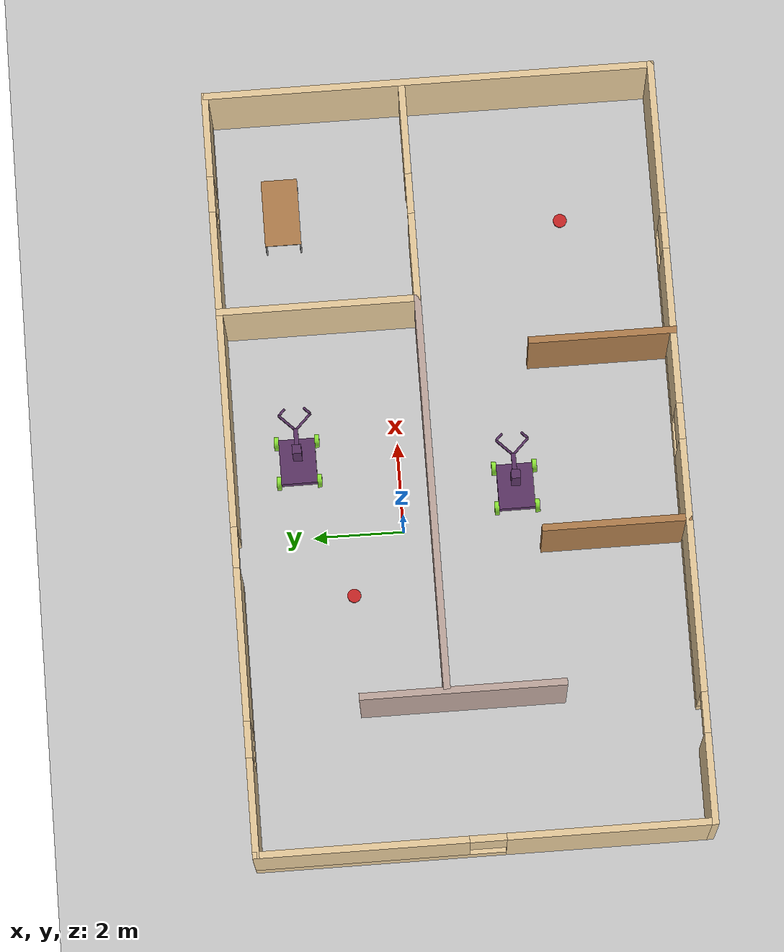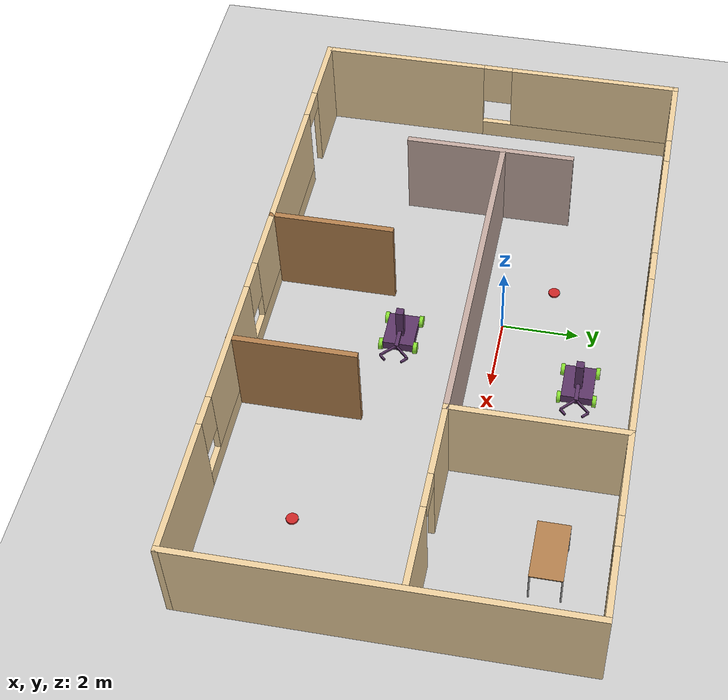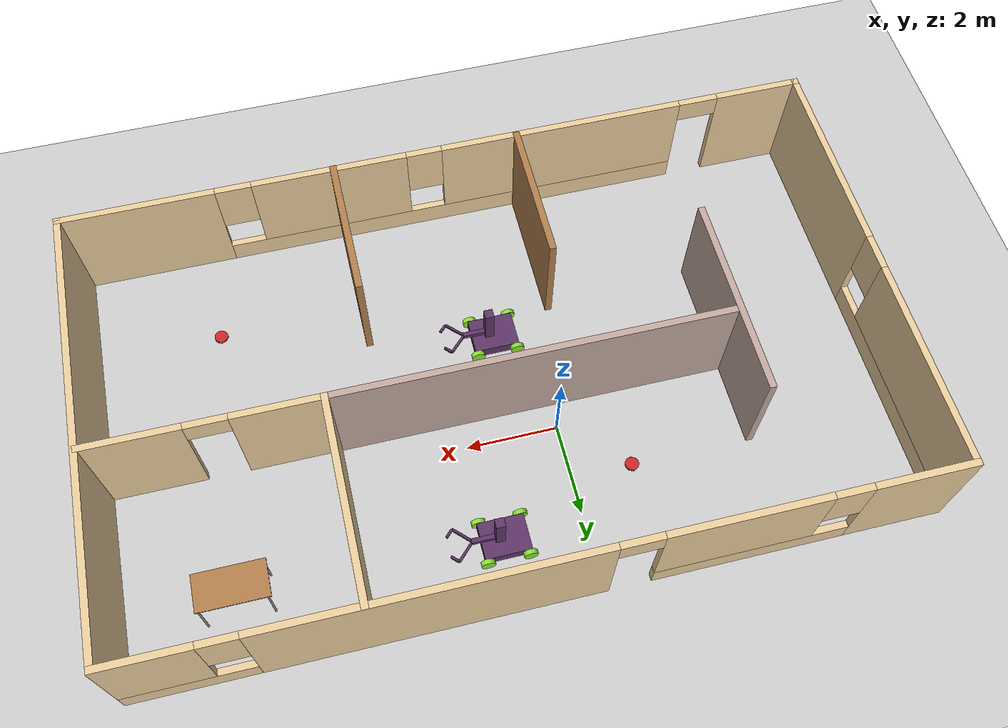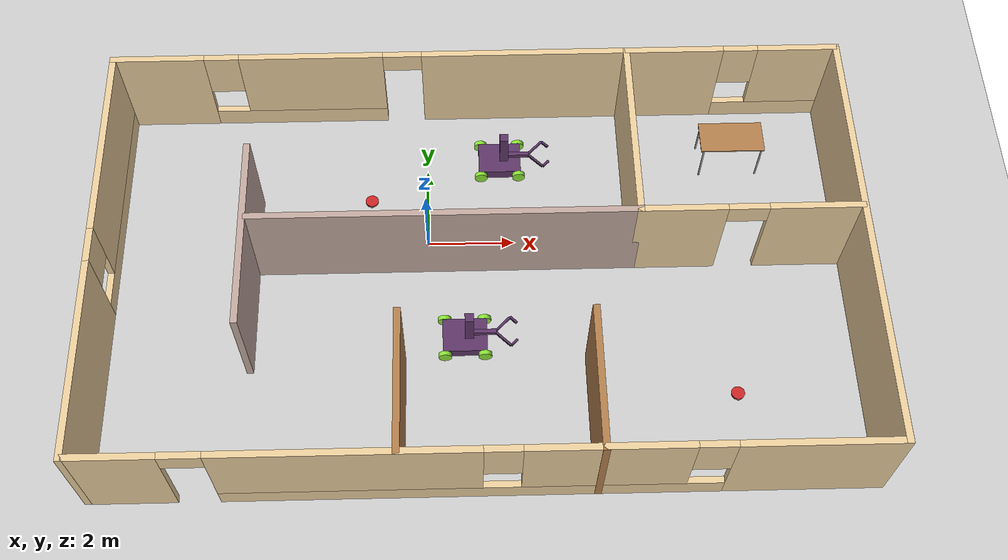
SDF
<sdf version="1.7">
 <world name="default">
  <plugin name="welcome_message" filename="libwelcome_message.so"/>
  <light name="sun" type="directional">
   <pose>0 0 10 0 -0 0</pose>
   <diffuse>0.8 0.8 0.8 1</diffuse>
   <specular>0.2 0.2 0.2 1</specular>
   <attenuation>
    <range>1000</range>
    <constant>0.9</constant>
    <linear>0.01</linear>
    <quadratic>0.001</quadratic>
   </attenuation>
   <direction>-0.5 0.1 -0.9</direction>
   <spot><inner_angle>0</inner_angle><outer_angle>0</outer_angle><falloff>0</falloff></spot>
  </light>
  <model name="ground_plane">
   <static>1</static>
   <link name="ground_link">
    <collision name="collision">
     <geometry><plane><normal>0 0 1</normal><size>100 100</size></plane></geometry>
     <surface><friction><ode><mu>100</mu><mu2>50</mu2></ode></friction></surface>
    </collision>
    <visual name="visual">
     <cast_shadows>0</cast_shadows>
     <geometry><plane><normal>0 0 1</normal><size>100 100</size></plane></geometry>
     <material>
      <script><uri>file://media/materials/scripts/gazebo.material</uri><name>Gazebo/Grey</name></script>
     </material>
    </visual>
   </link>
  </model>
  <gravity>0 0 -9.8</gravity>
  <magnetic_field>6e-06 2.3e-05 -4.2e-05</magnetic_field>
  <atmosphere type="adiabatic"/>
  <physics type="ode">
   <max_step_size>0.001</max_step_size>
   <real_time_factor>1</real_time_factor>
   <real_time_update_rate>1000</real_time_update_rate>
  </physics>
  <scene><ambient>0.4 0.4 0.4 1</ambient><background>0.7 0.7 0.7 1</background><shadows>1</shadows></scene>
  <spherical_coordinates>
   <surface_model>EARTH_WGS84</surface_model>
   <latitude_deg>0</latitude_deg>
   <longitude_deg>0</longitude_deg>
   <elevation>0</elevation>
   <heading_deg>0</heading_deg>
  </spherical_coordinates>
  <model name="HomeOffice">
   <pose>1.17907 -1.24904 0 0 -0 0</pose>
   <link name="Wall_0">
    <pose>-8.425 0.002596 0 0 -0 1.5708</pose>
    <visual name="Wall_0_Visual_0">
     <pose>-2.72763 0 1.25 0 -0 0</pose>
     <geometry><box><size>4.54474 0.15 2.5</size></box></geometry>
     <material>
      <script><uri>file://media/materials/scripts/gazebo.material</uri><name>Gazebo/Grey</name></script>
      <ambient>0.921569 0.807843 0.615686 1</ambient>
     </material>
     <meta><layer>0</layer></meta>
    </visual>
    <collision name="Wall_0_Collision_0">
     <geometry><box><size>4.54474 0.15 2.5</size></box></geometry>
     <pose>-2.72763 0 1.25 0 -0 0</pose>
    </collision>
    <visual name="Wall_0_Visual_1">
     <pose>2.27237 0 0.25 0 -0 0</pose>
     <geometry><box><size>5.45526 0.15 0.5</size></box></geometry>
     <material>
      <script><uri>file://media/materials/scripts/gazebo.material</uri><name>Gazebo/Grey</name></script>
      <ambient>0.921569 0.807843 0.615686 1</ambient>
     </material>
     <meta><layer>0</layer></meta>
    </visual>
    <collision name="Wall_0_Collision_1">
     <geometry><box><size>5.45526 0.15 0.5</size></box></geometry>
     <pose>2.27237 0 0.25 0 -0 0</pose>
    </collision>
    <visual name="Wall_0_Visual_2">
     <pose>2.67237 0 1.5 0 -0 0</pose>
     <geometry><box><size>4.65526 0.15 2</size></box></geometry>
     <material>
      <script><uri>file://media/materials/scripts/gazebo.material</uri><name>Gazebo/Grey</name></script>
      <ambient>0.921569 0.807843 0.615686 1</ambient>
     </material>
     <meta><layer>0</layer></meta>
    </visual>
    <collision name="Wall_0_Collision_2">
     <geometry><box><size>4.65526 0.15 2</size></box></geometry>
     <pose>2.67237 0 1.5 0 -0 0</pose>
    </collision>
    <visual name="Wall_0_Visual_3">
     <pose>-0.055255 0 1.9 0 -0 0</pose>
     <geometry><box><size>0.8 0.15 1.2</size></box></geometry>
     <material>
      <script><uri>file://media/materials/scripts/gazebo.material</uri><name>Gazebo/Grey</name></script>
      <ambient>0.921569 0.807843 0.615686 1</ambient>
     </material>
     <meta><layer>0</layer></meta>
    </visual>
    <collision name="Wall_0_Collision_3">
     <geometry><box><size>0.8 0.15 1.2</size></box></geometry>
     <pose>-0.055255 0 1.9 0 -0 0</pose>
    </collision>
   </link>
   <link name="Wall_1">
    <pose>-0 4.9276 0 0 -0 0</pose>
    <visual name="Wall_1_Visual_0">
     <pose>-7.41024 0 1.25 0 -0 0</pose>
     <geometry><box><size>2.17952 0.15 2.5</size></box></geometry>
     <material>
      <script><uri>file://media/materials/scripts/gazebo.material</uri><name>Gazebo/Grey</name></script>
      <ambient>0.921569 0.807843 0.615686 1</ambient>
     </material>
     <meta><layer>0</layer></meta>
    </visual>
    <collision name="Wall_1_Collision_0">
     <geometry><box><size>2.17952 0.15 2.5</size></box></geometry>
     <pose>-7.41024 0 1.25 0 -0 0</pose>
    </collision>
    <visual name="Wall_1_Visual_1">
     <pose>2.26645 0 1.25 0 -0 0</pose>
     <geometry><box><size>7.05766 0.15 2.5</size></box></geometry>
     <material>
      <script><uri>file://media/materials/scripts/gazebo.material</uri><name>Gazebo/Grey</name></script>
      <ambient>0.921569 0.807843 0.615686 1</ambient>
     </material>
     <meta><layer>0</layer></meta>
    </visual>
    <collision name="Wall_1_Collision_1">
     <geometry><box><size>7.05766 0.15 2.5</size></box></geometry>
     <pose>2.26645 0 1.25 0 -0 0</pose>
    </collision>
    <visual name="Wall_1_Visual_2">
     <pose>-4.24143 0 0.25 0 -0 0</pose>
     <geometry><box><size>4.1581 0.15 0.5</size></box></geometry>
     <material>
      <script><uri>file://media/materials/scripts/gazebo.material</uri><name>Gazebo/Grey</name></script>
      <ambient>0.921569 0.807843 0.615686 1</ambient>
     </material>
     <meta><layer>0</layer></meta>
    </visual>
    <collision name="Wall_1_Collision_2">
     <geometry><box><size>4.1581 0.15 0.5</size></box></geometry>
     <pose>-4.24143 0 0.25 0 -0 0</pose>
    </collision>
    <visual name="Wall_1_Visual_3">
     <pose>7.14764 0 0.25 0 -0 0</pose>
     <geometry><box><size>2.70472 0.15 0.5</size></box></geometry>
     <material>
      <script><uri>file://media/materials/scripts/gazebo.material</uri><name>Gazebo/Grey</name></script>
      <ambient>0.921569 0.807843 0.615686 1</ambient>
     </material>
     <meta><layer>0</layer></meta>
    </visual>
    <collision name="Wall_1_Collision_3">
     <geometry><box><size>2.70472 0.15 0.5</size></box></geometry>
     <pose>7.14764 0 0.25 0 -0 0</pose>
    </collision>
    <visual name="Wall_1_Visual_4">
     <pose>-3.84143 0 1.5 0 -0 0</pose>
     <geometry><box><size>3.3581 0.15 2</size></box></geometry>
     <material>
      <script><uri>file://media/materials/scripts/gazebo.material</uri><name>Gazebo/Grey</name></script>
      <ambient>0.921569 0.807843 0.615686 1</ambient>
     </material>
     <meta><layer>0</layer></meta>
    </visual>
    <collision name="Wall_1_Collision_4">
     <geometry><box><size>3.3581 0.15 2</size></box></geometry>
     <pose>-3.84143 0 1.5 0 -0 0</pose>
    </collision>
    <visual name="Wall_1_Visual_5">
     <pose>-3.84143 0 1.5 0 -0 0</pose>
     <geometry><box><size>3.3581 0.15 2</size></box></geometry>
     <material>
      <script><uri>file://media/materials/scripts/gazebo.material</uri><name>Gazebo/Grey</name></script>
      <ambient>0.921569 0.807843 0.615686 1</ambient>
     </material>
     <meta><layer>0</layer></meta>
    </visual>
    <collision name="Wall_1_Collision_5">
     <geometry><box><size>3.3581 0.15 2</size></box></geometry>
     <pose>-3.84143 0 1.5 0 -0 0</pose>
    </collision>
    <visual name="Wall_1_Visual_6">
     <pose>7.54764 0 1.5 0 -0 0</pose>
     <geometry><box><size>1.90472 0.15 2</size></box></geometry>
     <material>
      <script><uri>file://media/materials/scripts/gazebo.material</uri><name>Gazebo/Grey</name></script>
      <ambient>0.921569 0.807843 0.615686 1</ambient>
     </material>
     <meta><layer>0</layer></meta>
    </visual>
    <collision name="Wall_1_Collision_6">
     <geometry><box><size>1.90472 0.15 2</size></box></geometry>
     <pose>7.54764 0 1.5 0 -0 0</pose>
    </collision>
    <visual name="Wall_1_Visual_7">
     <pose>-5.92048 0 1.9 0 -0 0</pose>
     <geometry><box><size>0.8 0.15 1.2</size></box></geometry>
     <material>
      <script><uri>file://media/materials/scripts/gazebo.material</uri><name>Gazebo/Grey</name></script>
      <ambient>0.921569 0.807843 0.615686 1</ambient>
     </material>
     <meta><layer>0</layer></meta>
    </visual>
    <collision name="Wall_1_Collision_7">
     <geometry><box><size>0.8 0.15 1.2</size></box></geometry>
     <pose>-5.92048 0 1.9 0 -0 0</pose>
    </collision>
    <visual name="Wall_1_Visual_8">
     <pose>6.19528 0 1.9 0 -0 0</pose>
     <geometry><box><size>0.8 0.15 1.2</size></box></geometry>
     <material>
      <script><uri>file://media/materials/scripts/gazebo.material</uri><name>Gazebo/Grey</name></script>
      <ambient>0.921569 0.807843 0.615686 1</ambient>
     </material>
     <meta><layer>0</layer></meta>
    </visual>
    <collision name="Wall_1_Collision_8">
     <geometry><box><size>0.8 0.15 1.2</size></box></geometry>
     <pose>6.19528 0 1.9 0 -0 0</pose>
    </collision>
    <visual name="Wall_1_Visual_9">
     <pose>-1.71238 0 2.25 0 -0 0</pose>
     <geometry><box><size>0.9 0.15 0.5</size></box></geometry>
     <material>
      <script><uri>file://media/materials/scripts/gazebo.material</uri><name>Gazebo/Grey</name></script>
      <ambient>0.921569 0.807843 0.615686 1</ambient>
     </material>
     <meta><layer>0</layer></meta>
    </visual>
    <collision name="Wall_1_Collision_9">
     <geometry><box><size>0.9 0.15 0.5</size></box></geometry>
     <pose>-1.71238 0 2.25 0 -0 0</pose>
    </collision>
    <visual name="Wall_1_Visual_10">
     <pose>-1.71238 0 2.25 0 -0 0</pose>
     <geometry><box><size>0.9 0.15 0.5</size></box></geometry>
     <material>
      <script><uri>file://media/materials/scripts/gazebo.material</uri><name>Gazebo/Grey</name></script>
      <ambient>0.921569 0.807843 0.615686 1</ambient>
     </material>
     <meta><layer>0</layer></meta>
    </visual>
    <collision name="Wall_1_Collision_10">
     <geometry><box><size>0.9 0.15 0.5</size></box></geometry>
     <pose>-1.71238 0 2.25 0 -0 0</pose>
    </collision>
   </link>
   <link name="Wall_11">
    <pose>5.95103 0.586614 0 0 -0 0</pose>
    <visual name="Wall_11_Visual_0">
     <pose>-1.50527 0 1.25 0 -0 0</pose>
     <geometry><box><size>1.98945 0.15 2.5</size></box></geometry>
     <material>
      <script><uri>file://media/materials/scripts/gazebo.material</uri><name>Gazebo/Grey</name></script>
      <ambient>0.921569 0.807843 0.615686 1</ambient>
     </material>
     <meta><layer>0</layer></meta>
    </visual>
    <collision name="Wall_11_Collision_0">
     <geometry><box><size>1.98945 0.15 2.5</size></box></geometry>
     <pose>-1.50527 0 1.25 0 -0 0</pose>
    </collision>
    <visual name="Wall_11_Visual_1">
     <pose>1.44473 0 1.25 0 -0 0</pose>
     <geometry><box><size>2.11055 0.15 2.5</size></box></geometry>
     <material>
      <script><uri>file://media/materials/scripts/gazebo.material</uri><name>Gazebo/Grey</name></script>
      <ambient>0.921569 0.807843 0.615686 1</ambient>
     </material>
     <meta><layer>0</layer></meta>
    </visual>
    <collision name="Wall_11_Collision_1">
     <geometry><box><size>2.11055 0.15 2.5</size></box></geometry>
     <pose>1.44473 0 1.25 0 -0 0</pose>
    </collision>
    <visual name="Wall_11_Visual_2">
     <pose>-0.060545 0 2.25 0 -0 0</pose>
     <geometry><box><size>0.9 0.15 0.5</size></box></geometry>
     <material>
      <script><uri>file://media/materials/scripts/gazebo.material</uri><name>Gazebo/Grey</name></script>
      <ambient>0.921569 0.807843 0.615686 1</ambient>
     </material>
     <meta><layer>0</layer></meta>
    </visual>
    <collision name="Wall_11_Collision_2">
     <geometry><box><size>0.9 0.15 0.5</size></box></geometry>
     <pose>-0.060545 0 2.25 0 -0 0</pose>
    </collision>
   </link>
   <link name="Wall_15">
    <collision name="Wall_15_Collision">
     <geometry><box><size>3.25 0.15 2.5</size></box></geometry>
     <pose>0 0 1.25 0 -0 0</pose>
    </collision>
    <visual name="Wall_15_Visual">
     <pose>0 0 1.25 0 -0 0</pose>
     <geometry><box><size>3.25 0.15 2.5</size></box></geometry>
     <material>
      <script><uri>file://media/materials/scripts/gazebo.material</uri><name>Gazebo/Wood</name></script>
      <ambient>1 1 1 1</ambient>
     </material>
     <meta><layer>0</layer></meta>
    </visual>
    <pose>2.3971 -3.3776 0 0 -0 1.5708</pose>
   </link>
   <link name="Wall_17">
    <collision name="Wall_17_Collision">
     <geometry><box><size>3.25 0.15 2.5</size></box></geometry>
     <pose>0 0 1.25 0 -0 0</pose>
    </collision>
    <visual name="Wall_17_Visual">
     <pose>0 0 1.25 0 -0 0</pose>
     <geometry><box><size>3.25 0.15 2.5</size></box></geometry>
     <material>
      <script><uri>file://media/materials/scripts/gazebo.material</uri><name>Gazebo/Wood</name></script>
      <ambient>1 1 1 1</ambient>
     </material>
     <meta><layer>0</layer></meta>
    </visual>
    <pose>-1.77936 -3.35562 0 0 -0 1.5708</pose>
   </link>
   <link name="Wall_2">
    <collision name="Wall_2_Collision">
     <geometry><box><size>10 0.15 2.5</size></box></geometry>
     <pose>0 0 1.25 0 -0 0</pose>
    </collision>
    <visual name="Wall_2_Visual">
     <pose>0 0 1.25 0 -0 0</pose>
     <geometry><box><size>10 0.15 2.5</size></box></geometry>
     <material>
      <script><uri>file://media/materials/scripts/gazebo.material</uri><name>Gazebo/Grey</name></script>
      <ambient>0.921569 0.807843 0.615686 1</ambient>
     </material>
     <meta><layer>0</layer></meta>
    </visual>
    <pose>8.425 0.002596 0 0 -0 -1.5708</pose>
   </link>
   <link name="Wall_3">
    <pose>-0 -4.9224 0 0 -0 3.14159</pose>
    <visual name="Wall_3_Visual_0">
     <pose>-6.76663 0 1.25 0 -0 0</pose>
     <geometry><box><size>3.46674 0.15 2.5</size></box></geometry>
     <material>
      <script><uri>file://media/materials/scripts/gazebo.material</uri><name>Gazebo/Grey</name></script>
      <ambient>0.921569 0.807843 0.615686 1</ambient>
     </material>
     <meta><layer>0</layer></meta>
    </visual>
    <collision name="Wall_3_Collision_0">
     <geometry><box><size>3.46674 0.15 2.5</size></box></geometry>
     <pose>-6.76663 0 1.25 0 -0 0</pose>
    </collision>
    <visual name="Wall_3_Visual_1">
     <pose>7.5069 0 1.25 0 -0 0</pose>
     <geometry><box><size>1.98621 0.15 2.5</size></box></geometry>
     <material>
      <script><uri>file://media/materials/scripts/gazebo.material</uri><name>Gazebo/Grey</name></script>
      <ambient>0.921569 0.807843 0.615686 1</ambient>
     </material>
     <meta><layer>0</layer></meta>
    </visual>
    <collision name="Wall_3_Collision_1">
     <geometry><box><size>1.98621 0.15 2.5</size></box></geometry>
     <pose>7.5069 0 1.25 0 -0 0</pose>
    </collision>
    <visual name="Wall_3_Visual_2">
     <pose>0.290267 0 0.25 0 -0 0</pose>
     <geometry><box><size>10.6471 0.15 0.5</size></box></geometry>
     <material>
      <script><uri>file://media/materials/scripts/gazebo.material</uri><name>Gazebo/Grey</name></script>
      <ambient>0.921569 0.807843 0.615686 1</ambient>
     </material>
     <meta><layer>0</layer></meta>
    </visual>
    <collision name="Wall_3_Collision_2">
     <geometry><box><size>10.6471 0.15 0.5</size></box></geometry>
     <pose>0.290267 0 0.25 0 -0 0</pose>
    </collision>
    <visual name="Wall_3_Visual_3">
     <pose>-2.49467 0 1.5 0 -0 0</pose>
     <geometry><box><size>3.47717 0.15 2</size></box></geometry>
     <material>
      <script><uri>file://media/materials/scripts/gazebo.material</uri><name>Gazebo/Grey</name></script>
      <ambient>0.921569 0.807843 0.615686 1</ambient>
     </material>
     <meta><layer>0</layer></meta>
    </visual>
    <collision name="Wall_3_Collision_3">
     <geometry><box><size>3.47717 0.15 2</size></box></geometry>
     <pose>-2.49467 0 1.5 0 -0 0</pose>
    </collision>
    <visual name="Wall_3_Visual_4">
     <pose>2.82885 0 1.5 0 -0 0</pose>
     <geometry><box><size>5.56988 0.15 2</size></box></geometry>
     <material>
      <script><uri>file://media/materials/scripts/gazebo.material</uri><name>Gazebo/Grey</name></script>
      <ambient>0.921569 0.807843 0.615686 1</ambient>
     </material>
     <meta><layer>0</layer></meta>
    </visual>
    <collision name="Wall_3_Collision_4">
     <geometry><box><size>5.56988 0.15 2</size></box></geometry>
     <pose>2.82885 0 1.5 0 -0 0</pose>
    </collision>
    <visual name="Wall_3_Visual_5">
     <pose>-4.63326 0 1.9 0 -0 0</pose>
     <geometry><box><size>0.8 0.15 1.2</size></box></geometry>
     <material>
      <script><uri>file://media/materials/scripts/gazebo.material</uri><name>Gazebo/Grey</name></script>
      <ambient>0.921569 0.807843 0.615686 1</ambient>
     </material>
     <meta><layer>0</layer></meta>
    </visual>
    <collision name="Wall_3_Collision_5">
     <geometry><box><size>0.8 0.15 1.2</size></box></geometry>
     <pose>-4.63326 0 1.9 0 -0 0</pose>
    </collision>
    <visual name="Wall_3_Visual_6">
     <pose>-0.356089 0 1.9 0 -0 0</pose>
     <geometry><box><size>0.8 0.15 1.2</size></box></geometry>
     <material>
      <script><uri>file://media/materials/scripts/gazebo.material</uri><name>Gazebo/Grey</name></script>
      <ambient>0.921569 0.807843 0.615686 1</ambient>
     </material>
     <meta><layer>0</layer></meta>
    </visual>
    <collision name="Wall_3_Collision_6">
     <geometry><box><size>0.8 0.15 1.2</size></box></geometry>
     <pose>-0.356089 0 1.9 0 -0 0</pose>
    </collision>
    <visual name="Wall_3_Visual_7">
     <pose>6.06379 0 2.25 0 -0 0</pose>
     <geometry><box><size>0.9 0.15 0.5</size></box></geometry>
     <material>
      <script><uri>file://media/materials/scripts/gazebo.material</uri><name>Gazebo/Grey</name></script>
      <ambient>0.921569 0.807843 0.615686 1</ambient>
     </material>
     <meta><layer>0</layer></meta>
    </visual>
    <collision name="Wall_3_Collision_7">
     <geometry><box><size>0.9 0.15 0.5</size></box></geometry>
     <pose>6.06379 0 2.25 0 -0 0</pose>
    </collision>
   </link>
   <link name="Wall_5">
    <collision name="Wall_5_Collision">
     <geometry><box><size>4.5 0.15 2.5</size></box></geometry>
     <pose>0 0 1.25 0 -0 0</pose>
    </collision>
    <visual name="Wall_5_Visual">
     <pose>0 0 1.25 0 -0 0</pose>
     <geometry><box><size>4.5 0.15 2.5</size></box></geometry>
     <material>
      <script><uri>file://media/materials/scripts/gazebo.material</uri><name>Gazebo/Grey</name></script>
      <ambient>0.760784 0.662745 0.627451 1</ambient>
     </material>
     <meta><layer>0</layer></meta>
    </visual>
    <pose>-5.17438 0.236386 0 0 -0 -1.5708</pose>
   </link>
   <link name="Wall_8">
    <collision name="Wall_8_Collision">
     <geometry><box><size>8.75 0.15 2.5</size></box></geometry>
     <pose>0 0 1.25 0 -0 0</pose>
    </collision>
    <visual name="Wall_8_Visual">
     <pose>0 0 1.25 0 -0 0</pose>
     <geometry><box><size>8.75 0.15 2.5</size></box></geometry>
     <material>
      <script><uri>file://media/materials/scripts/gazebo.material</uri><name>Gazebo/Grey</name></script>
      <ambient>0.760784 0.662745 0.627451 1</ambient>
     </material>
     <meta><layer>0</layer></meta>
    </visual>
    <pose>-0.773966 0.586614 0 0 -0 0</pose>
   </link>
   <link name="Wall_9">
    <collision name="Wall_9_Collision">
     <geometry><box><size>4.48714 0.15 2.5</size></box></geometry>
     <pose>0 0 1.25 0 -0 0</pose>
    </collision>
    <visual name="Wall_9_Visual">
     <pose>0 0 1.25 0 -0 0</pose>
     <geometry><box><size>4.48714 0.15 2.5</size></box></geometry>
     <material>
      <script><uri>file://media/materials/scripts/gazebo.material</uri><name>Gazebo/Grey</name></script>
      <ambient>0.921569 0.807843 0.615686 1</ambient>
     </material>
     <meta><layer>0</layer></meta>
    </visual>
    <pose>3.52603 2.75519 0 0 -0 1.5708</pose>
   </link>
   <static>1</static>
  </model>
  <model name="CleanerBot">
   <link name="link_0">
    <inertial>
     <mass>1</mass>
     <inertia><ixx>0.145833</ixx><ixy>0</ixy><ixz>0</ixz><iyy>0.145833</iyy><iyz>0</iyz><izz>0.125</izz></inertia>
    </inertial>
    <pose>0 0 0.012 0 -0 0</pose>
    <visual name="visual">
     <geometry><cylinder><radius>0.15</radius><length>0.05</length></cylinder></geometry>
     <material>
      <lighting>1</lighting>
      <script><uri>file://media/materials/scripts/gazebo.material</uri><name>Gazebo/Red</name></script>
      <shader type="pixel"><normal_map>__default__</normal_map></shader>
      <ambient>0.8 0 0 1</ambient>
      <diffuse>0.7 0.7 0.7 1</diffuse>
      <specular>0.01 0.01 0.01 1</specular>
      <emissive>0 0 0 1</emissive>
     </material>
    </visual>
    <collision name="collision">
     <geometry><cylinder><radius>0.15</radius><length>0.05</length></cylinder></geometry>
     <surface>
      <friction>
       <ode><mu>1</mu><mu2>1</mu2><fdir1>0 0 0</fdir1><slip1>0</slip1><slip2>0</slip2></ode>
       <torsional>
        <coefficient>1</coefficient>
        <patch_radius>0</patch_radius>
        <surface_radius>0</surface_radius>
        <use_patch_radius>1</use_patch_radius>
        <ode><slip>0</slip></ode>
       </torsional>
      </friction>
      <bounce><restitution_coefficient>0</restitution_coefficient><threshold>1e+06</threshold></bounce>
      <contact>
       <collide_without_contact>0</collide_without_contact>
       <collide_without_contact_bitmask>1</collide_without_contact_bitmask>
       <collide_bitmask>1</collide_bitmask>
       <ode>
        <soft_cfm>0</soft_cfm>
        <soft_erp>0.2</soft_erp>
        <kp>1e+13</kp>
        <kd>1</kd>
        <max_vel>0.01</max_vel>
        <min_depth>0</min_depth>
       </ode>
       <bullet>
        <split_impulse>1</split_impulse>
        <split_impulse_penetration_threshold>-0.01</split_impulse_penetration_threshold>
        <soft_cfm>0</soft_cfm>
        <soft_erp>0.2</soft_erp>
        <kp>1e+13</kp>
        <kd>1</kd>
       </bullet>
      </contact>
     </surface>
    </collision>
   </link>
   <link name="link_1">
    <inertial>
     <mass>1</mass>
     <inertia><ixx>0.145833</ixx><ixy>0</ixy><ixz>0</ixz><iyy>0.145833</iyy><iyz>0</iyz><izz>0.125</izz></inertia>
    </inertial>
    <pose>0 0.15 0.007 1.5707 -0 0</pose>
    <visual name="visual">
     <geometry><cylinder><radius>0.03</radius><length>0.01</length></cylinder></geometry>
     <material>
      <lighting>1</lighting>
      <script><uri>file://media/materials/scripts/gazebo.material</uri><name>Gazebo/Black</name></script>
      <shader type="pixel"><normal_map>__default__</normal_map></shader>
      <ambient>0 0 0.8 1</ambient>
      <diffuse>0.7 0.7 0.7 1</diffuse>
      <specular>0.01 0.01 0.01 1</specular>
      <emissive>0 0 0 1</emissive>
     </material>
    </visual>
    <collision name="collision">
     <geometry><cylinder><radius>0.03</radius><length>0.01</length></cylinder></geometry>
     <surface>
      <friction>
       <ode><mu>1</mu><mu2>1</mu2><fdir1>0 0 0</fdir1><slip1>0</slip1><slip2>0</slip2></ode>
       <torsional>
        <coefficient>1</coefficient>
        <patch_radius>0</patch_radius>
        <surface_radius>0</surface_radius>
        <use_patch_radius>1</use_patch_radius>
        <ode><slip>0</slip></ode>
       </torsional>
      </friction>
      <bounce><restitution_coefficient>0</restitution_coefficient><threshold>1e+06</threshold></bounce>
      <contact>
       <collide_without_contact>0</collide_without_contact>
       <collide_without_contact_bitmask>1</collide_without_contact_bitmask>
       <collide_bitmask>1</collide_bitmask>
       <ode>
        <soft_cfm>0</soft_cfm>
        <soft_erp>0.2</soft_erp>
        <kp>1e+13</kp>
        <kd>1</kd>
        <max_vel>0.01</max_vel>
        <min_depth>0</min_depth>
       </ode>
       <bullet>
        <split_impulse>1</split_impulse>
        <split_impulse_penetration_threshold>-0.01</split_impulse_penetration_threshold>
        <soft_cfm>0</soft_cfm>
        <soft_erp>0.2</soft_erp>
        <kp>1e+13</kp>
        <kd>1</kd>
       </bullet>
      </contact>
     </surface>
    </collision>
   </link>
   <link name="link_1_clone">
    <inertial>
     <mass>1</mass>
     <inertia><ixx>0.145833</ixx><ixy>0</ixy><ixz>0</ixz><iyy>0.145833</iyy><iyz>0</iyz><izz>0.125</izz></inertia>
    </inertial>
    <pose>0 -0.15 0.007 1.5707 -0 0</pose>
    <visual name="visual">
     <geometry><cylinder><radius>0.03</radius><length>0.01</length></cylinder></geometry>
     <material>
      <lighting>1</lighting>
      <script><uri>file://media/materials/scripts/gazebo.material</uri><name>Gazebo/Black</name></script>
      <shader type="pixel"><normal_map>__default__</normal_map></shader>
      <ambient>0 0 0.8 1</ambient>
      <diffuse>0.7 0.7 0.7 1</diffuse>
      <specular>0.01 0.01 0.01 1</specular>
      <emissive>0 0 0 1</emissive>
     </material>
    </visual>
    <collision name="collision">
     <geometry><cylinder><radius>0.03</radius><length>0.01</length></cylinder></geometry>
     <surface>
      <friction>
       <ode><mu>1</mu><mu2>1</mu2><fdir1>0 0 0</fdir1><slip1>0</slip1><slip2>0</slip2></ode>
       <torsional>
        <coefficient>1</coefficient>
        <patch_radius>0</patch_radius>
        <surface_radius>0</surface_radius>
        <use_patch_radius>1</use_patch_radius>
        <ode><slip>0</slip></ode>
       </torsional>
      </friction>
      <bounce><restitution_coefficient>0</restitution_coefficient><threshold>1e+06</threshold></bounce>
      <contact>
       <collide_without_contact>0</collide_without_contact>
       <collide_without_contact_bitmask>1</collide_without_contact_bitmask>
       <collide_bitmask>1</collide_bitmask>
       <ode>
        <soft_cfm>0</soft_cfm>
        <soft_erp>0.2</soft_erp>
        <kp>1e+13</kp>
        <kd>1</kd>
        <max_vel>0.01</max_vel>
        <min_depth>0</min_depth>
       </ode>
       <bullet>
        <split_impulse>1</split_impulse>
        <split_impulse_penetration_threshold>-0.01</split_impulse_penetration_threshold>
        <soft_cfm>0</soft_cfm>
        <soft_erp>0.2</soft_erp>
        <kp>1e+13</kp>
        <kd>1</kd>
       </bullet>
      </contact>
     </surface>
    </collision>
   </link>
   <link name="link_2">
    <inertial>
     <mass>1</mass>
     <inertia><ixx>0.1</ixx><ixy>0</ixy><ixz>0</ixz><iyy>0.1</iyy><iyz>0</iyz><izz>0.1</izz></inertia>
    </inertial>
    <pose>0.13 0 -0.013 0 -0 0</pose>
    <visual name="visual">
     <geometry><sphere><radius>0.01</radius></sphere></geometry>
     <material>
      <lighting>1</lighting>
      <script><uri>file://media/materials/scripts/gazebo.material</uri><name>Gazebo/Grey</name></script>
      <shader type="pixel"><normal_map>__default__</normal_map></shader>
      <ambient>0.3 0.3 0.3 1</ambient>
      <diffuse>0.7 0.7 0.7 1</diffuse>
      <specular>0.01 0.01 0.01 1</specular>
      <emissive>0 0 0 1</emissive>
     </material>
    </visual>
    <collision name="collision">
     <geometry><sphere><radius>0.01</radius></sphere></geometry>
     <surface>
      <friction>
       <ode><mu>0</mu><mu2>0</mu2><fdir1>0 0 0</fdir1><slip1>0</slip1><slip2>0</slip2></ode>
       <torsional>
        <coefficient>1</coefficient>
        <patch_radius>0</patch_radius>
        <surface_radius>0</surface_radius>
        <use_patch_radius>1</use_patch_radius>
        <ode><slip>0</slip></ode>
       </torsional>
      </friction>
      <bounce><restitution_coefficient>0</restitution_coefficient><threshold>1e+06</threshold></bounce>
      <contact>
       <collide_without_contact>0</collide_without_contact>
       <collide_without_contact_bitmask>1</collide_without_contact_bitmask>
       <collide_bitmask>1</collide_bitmask>
       <ode>
        <soft_cfm>0</soft_cfm>
        <soft_erp>0.2</soft_erp>
        <kp>1e+13</kp>
        <kd>1</kd>
        <max_vel>0.01</max_vel>
        <min_depth>0</min_depth>
       </ode>
       <bullet>
        <split_impulse>1</split_impulse>
        <split_impulse_penetration_threshold>-0.01</split_impulse_penetration_threshold>
        <soft_cfm>0</soft_cfm>
        <soft_erp>0.2</soft_erp>
        <kp>1e+13</kp>
        <kd>1</kd>
       </bullet>
      </contact>
     </surface>
    </collision>
   </link>
   <link name="link_2_clone">
    <inertial>
     <mass>1</mass>
     <inertia><ixx>0.1</ixx><ixy>0</ixy><ixz>0</ixz><iyy>0.1</iyy><iyz>0</iyz><izz>0.1</izz></inertia>
    </inertial>
    <pose>-0.13 0 -0.013 0 -0 0</pose>
    <visual name="visual">
     <geometry><sphere><radius>0.01</radius></sphere></geometry>
     <material>
      <lighting>1</lighting>
      <script><uri>file://media/materials/scripts/gazebo.material</uri><name>Gazebo/Grey</name></script>
      <shader type="pixel"><normal_map>__default__</normal_map></shader>
      <ambient>0.3 0.3 0.3 1</ambient>
      <diffuse>0.7 0.7 0.7 1</diffuse>
      <specular>0.01 0.01 0.01 1</specular>
      <emissive>0 0 0 1</emissive>
     </material>
    </visual>
    <collision name="collision">
     <geometry><sphere><radius>0.01</radius></sphere></geometry>
     <surface>
      <friction>
       <ode><mu>0</mu><mu2>0</mu2><fdir1>0 0 0</fdir1><slip1>0</slip1><slip2>0</slip2></ode>
       <torsional>
        <coefficient>1</coefficient>
        <patch_radius>0</patch_radius>
        <surface_radius>0</surface_radius>
        <use_patch_radius>1</use_patch_radius>
        <ode><slip>0</slip></ode>
       </torsional>
      </friction>
      <bounce><restitution_coefficient>0</restitution_coefficient><threshold>1e+06</threshold></bounce>
      <contact>
       <collide_without_contact>0</collide_without_contact>
       <collide_without_contact_bitmask>1</collide_without_contact_bitmask>
       <collide_bitmask>1</collide_bitmask>
       <ode>
        <soft_cfm>0</soft_cfm>
        <soft_erp>0.2</soft_erp>
        <kp>1e+13</kp>
        <kd>1</kd>
        <max_vel>0.01</max_vel>
        <min_depth>0</min_depth>
       </ode>
       <bullet>
        <split_impulse>1</split_impulse>
        <split_impulse_penetration_threshold>-0.01</split_impulse_penetration_threshold>
        <soft_cfm>0</soft_cfm>
        <soft_erp>0.2</soft_erp>
        <kp>1e+13</kp>
        <kd>1</kd>
       </bullet>
      </contact>
     </surface>
    </collision>
   </link>
   <joint name="link_0_JOINT_1" type="revolute">
    <parent>link_0</parent>
    <child>link_1_clone</child>
    <axis>
     <xyz>0 0 1</xyz>
     <limit>
      <lower>-1.79769e+308</lower>
      <upper>1.79769e+308</upper>
      <effort>-1</effort>
      <velocity>-1</velocity>
     </limit>
     <dynamics>
      <spring_reference>0</spring_reference>
      <spring_stiffness>0</spring_stiffness>
      <damping>0</damping>
     </dynamics>
    </axis>
    <physics>
     <ode><limit><cfm>0</cfm><erp>0.2</erp></limit><suspension><cfm>0</cfm><erp>0.2</erp></suspension></ode>
    </physics>
   </joint>
   <joint name="link_0_JOINT_2" type="revolute">
    <parent>link_0</parent>
    <child>link_1</child>
    <axis>
     <xyz>0 0 1</xyz>
     <limit>
      <lower>-1.79769e+308</lower>
      <upper>1.79769e+308</upper>
      <effort>-1</effort>
      <velocity>-1</velocity>
     </limit>
     <dynamics>
      <spring_reference>0</spring_reference>
      <spring_stiffness>0</spring_stiffness>
      <damping>0</damping>
     </dynamics>
    </axis>
    <physics>
     <ode><limit><cfm>0</cfm><erp>0.2</erp></limit><suspension><cfm>0</cfm><erp>0.2</erp></suspension></ode>
    </physics>
   </joint>
   <joint name="link_0_JOINT_4" type="fixed">
    <parent>link_0</parent>
    <child>link_2</child>
    <physics>
     <ode><limit><cfm>0</cfm><erp>0.2</erp></limit><suspension><cfm>0</cfm><erp>0.2</erp></suspension></ode>
    </physics>
   </joint>
   <joint name="link_0_JOINT_5" type="fixed">
    <parent>link_0</parent>
    <child>link_2_clone</child>
    <physics>
     <ode><limit><cfm>0</cfm><erp>0.2</erp></limit><suspension><cfm>0</cfm><erp>0.2</erp></suspension></ode>
    </physics>
   </joint>
   <static>0</static>
   <pose>6.82843 -3.99994 0.022999 9e-06 -2e-06 -0.003466</pose>
  </model>
  <model name="CleanerBot_0">
   <link name="link_0">
    <inertial>
     <mass>1</mass>
     <inertia><ixx>0.145833</ixx><ixy>0</ixy><ixz>0</ixz><iyy>0.145833</iyy><iyz>0</iyz><izz>0.125</izz></inertia>
    </inertial>
    <pose>0 0 0.012 0 -0 0</pose>
    <visual name="visual">
     <geometry><cylinder><radius>0.15</radius><length>0.05</length></cylinder></geometry>
     <material>
      <lighting>1</lighting>
      <script><uri>file://media/materials/scripts/gazebo.material</uri><name>Gazebo/Red</name></script>
      <shader type="pixel"><normal_map>__default__</normal_map></shader>
      <ambient>0.8 0 0 1</ambient>
      <diffuse>0.7 0.7 0.7 1</diffuse>
      <specular>0.01 0.01 0.01 1</specular>
      <emissive>0 0 0 1</emissive>
     </material>
    </visual>
    <collision name="collision">
     <geometry><cylinder><radius>0.15</radius><length>0.05</length></cylinder></geometry>
     <surface>
      <friction>
       <ode><mu>1</mu><mu2>1</mu2><fdir1>0 0 0</fdir1><slip1>0</slip1><slip2>0</slip2></ode>
       <torsional>
        <coefficient>1</coefficient>
        <patch_radius>0</patch_radius>
        <surface_radius>0</surface_radius>
        <use_patch_radius>1</use_patch_radius>
        <ode><slip>0</slip></ode>
       </torsional>
      </friction>
      <bounce><restitution_coefficient>0</restitution_coefficient><threshold>1e+06</threshold></bounce>
      <contact>
       <collide_without_contact>0</collide_without_contact>
       <collide_without_contact_bitmask>1</collide_without_contact_bitmask>
       <collide_bitmask>1</collide_bitmask>
       <ode>
        <soft_cfm>0</soft_cfm>
        <soft_erp>0.2</soft_erp>
        <kp>1e+13</kp>
        <kd>1</kd>
        <max_vel>0.01</max_vel>
        <min_depth>0</min_depth>
       </ode>
       <bullet>
        <split_impulse>1</split_impulse>
        <split_impulse_penetration_threshold>-0.01</split_impulse_penetration_threshold>
        <soft_cfm>0</soft_cfm>
        <soft_erp>0.2</soft_erp>
        <kp>1e+13</kp>
        <kd>1</kd>
       </bullet>
      </contact>
     </surface>
    </collision>
   </link>
   <link name="link_1">
    <inertial>
     <mass>1</mass>
     <inertia><ixx>0.145833</ixx><ixy>0</ixy><ixz>0</ixz><iyy>0.145833</iyy><iyz>0</iyz><izz>0.125</izz></inertia>
    </inertial>
    <pose>0 0.15 0.007 1.5707 -0 0</pose>
    <visual name="visual">
     <geometry><cylinder><radius>0.03</radius><length>0.01</length></cylinder></geometry>
     <material>
      <lighting>1</lighting>
      <script><uri>file://media/materials/scripts/gazebo.material</uri><name>Gazebo/Black</name></script>
      <shader type="pixel"><normal_map>__default__</normal_map></shader>
      <ambient>0 0 0.8 1</ambient>
      <diffuse>0.7 0.7 0.7 1</diffuse>
      <specular>0.01 0.01 0.01 1</specular>
      <emissive>0 0 0 1</emissive>
     </material>
    </visual>
    <collision name="collision">
     <geometry><cylinder><radius>0.03</radius><length>0.01</length></cylinder></geometry>
     <surface>
      <friction>
       <ode><mu>1</mu><mu2>1</mu2><fdir1>0 0 0</fdir1><slip1>0</slip1><slip2>0</slip2></ode>
       <torsional>
        <coefficient>1</coefficient>
        <patch_radius>0</patch_radius>
        <surface_radius>0</surface_radius>
        <use_patch_radius>1</use_patch_radius>
        <ode><slip>0</slip></ode>
       </torsional>
      </friction>
      <bounce><restitution_coefficient>0</restitution_coefficient><threshold>1e+06</threshold></bounce>
      <contact>
       <collide_without_contact>0</collide_without_contact>
       <collide_without_contact_bitmask>1</collide_without_contact_bitmask>
       <collide_bitmask>1</collide_bitmask>
       <ode>
        <soft_cfm>0</soft_cfm>
        <soft_erp>0.2</soft_erp>
        <kp>1e+13</kp>
        <kd>1</kd>
        <max_vel>0.01</max_vel>
        <min_depth>0</min_depth>
       </ode>
       <bullet>
        <split_impulse>1</split_impulse>
        <split_impulse_penetration_threshold>-0.01</split_impulse_penetration_threshold>
        <soft_cfm>0</soft_cfm>
        <soft_erp>0.2</soft_erp>
        <kp>1e+13</kp>
        <kd>1</kd>
       </bullet>
      </contact>
     </surface>
    </collision>
   </link>
   <link name="link_1_clone">
    <inertial>
     <mass>1</mass>
     <inertia><ixx>0.145833</ixx><ixy>0</ixy><ixz>0</ixz><iyy>0.145833</iyy><iyz>0</iyz><izz>0.125</izz></inertia>
    </inertial>
    <pose>0 -0.15 0.007 1.5707 -0 0</pose>
    <visual name="visual">
     <geometry><cylinder><radius>0.03</radius><length>0.01</length></cylinder></geometry>
     <material>
      <lighting>1</lighting>
      <script><uri>file://media/materials/scripts/gazebo.material</uri><name>Gazebo/Black</name></script>
      <shader type="pixel"><normal_map>__default__</normal_map></shader>
      <ambient>0 0 0.8 1</ambient>
      <diffuse>0.7 0.7 0.7 1</diffuse>
      <specular>0.01 0.01 0.01 1</specular>
      <emissive>0 0 0 1</emissive>
     </material>
    </visual>
    <collision name="collision">
     <geometry><cylinder><radius>0.03</radius><length>0.01</length></cylinder></geometry>
     <surface>
      <friction>
       <ode><mu>1</mu><mu2>1</mu2><fdir1>0 0 0</fdir1><slip1>0</slip1><slip2>0</slip2></ode>
       <torsional>
        <coefficient>1</coefficient>
        <patch_radius>0</patch_radius>
        <surface_radius>0</surface_radius>
        <use_patch_radius>1</use_patch_radius>
        <ode><slip>0</slip></ode>
       </torsional>
      </friction>
      <bounce><restitution_coefficient>0</restitution_coefficient><threshold>1e+06</threshold></bounce>
      <contact>
       <collide_without_contact>0</collide_without_contact>
       <collide_without_contact_bitmask>1</collide_without_contact_bitmask>
       <collide_bitmask>1</collide_bitmask>
       <ode>
        <soft_cfm>0</soft_cfm>
        <soft_erp>0.2</soft_erp>
        <kp>1e+13</kp>
        <kd>1</kd>
        <max_vel>0.01</max_vel>
        <min_depth>0</min_depth>
       </ode>
       <bullet>
        <split_impulse>1</split_impulse>
        <split_impulse_penetration_threshold>-0.01</split_impulse_penetration_threshold>
        <soft_cfm>0</soft_cfm>
        <soft_erp>0.2</soft_erp>
        <kp>1e+13</kp>
        <kd>1</kd>
       </bullet>
      </contact>
     </surface>
    </collision>
   </link>
   <link name="link_2">
    <inertial>
     <mass>1</mass>
     <inertia><ixx>0.1</ixx><ixy>0</ixy><ixz>0</ixz><iyy>0.1</iyy><iyz>0</iyz><izz>0.1</izz></inertia>
    </inertial>
    <pose>0.13 0 -0.013 0 -0 0</pose>
    <visual name="visual">
     <geometry><sphere><radius>0.01</radius></sphere></geometry>
     <material>
      <lighting>1</lighting>
      <script><uri>file://media/materials/scripts/gazebo.material</uri><name>Gazebo/Grey</name></script>
      <shader type="pixel"><normal_map>__default__</normal_map></shader>
      <ambient>0.3 0.3 0.3 1</ambient>
      <diffuse>0.7 0.7 0.7 1</diffuse>
      <specular>0.01 0.01 0.01 1</specular>
      <emissive>0 0 0 1</emissive>
     </material>
    </visual>
    <collision name="collision">
     <geometry><sphere><radius>0.01</radius></sphere></geometry>
     <surface>
      <friction>
       <ode><mu>0</mu><mu2>0</mu2><fdir1>0 0 0</fdir1><slip1>0</slip1><slip2>0</slip2></ode>
       <torsional>
        <coefficient>1</coefficient>
        <patch_radius>0</patch_radius>
        <surface_radius>0</surface_radius>
        <use_patch_radius>1</use_patch_radius>
        <ode><slip>0</slip></ode>
       </torsional>
      </friction>
      <bounce><restitution_coefficient>0</restitution_coefficient><threshold>1e+06</threshold></bounce>
      <contact>
       <collide_without_contact>0</collide_without_contact>
       <collide_without_contact_bitmask>1</collide_without_contact_bitmask>
       <collide_bitmask>1</collide_bitmask>
       <ode>
        <soft_cfm>0</soft_cfm>
        <soft_erp>0.2</soft_erp>
        <kp>1e+13</kp>
        <kd>1</kd>
        <max_vel>0.01</max_vel>
        <min_depth>0</min_depth>
       </ode>
       <bullet>
        <split_impulse>1</split_impulse>
        <split_impulse_penetration_threshold>-0.01</split_impulse_penetration_threshold>
        <soft_cfm>0</soft_cfm>
        <soft_erp>0.2</soft_erp>
        <kp>1e+13</kp>
        <kd>1</kd>
       </bullet>
      </contact>
     </surface>
    </collision>
   </link>
   <link name="link_2_clone">
    <inertial>
     <mass>1</mass>
     <inertia><ixx>0.1</ixx><ixy>0</ixy><ixz>0</ixz><iyy>0.1</iyy><iyz>0</iyz><izz>0.1</izz></inertia>
    </inertial>
    <pose>-0.13 0 -0.013 0 -0 0</pose>
    <visual name="visual">
     <geometry><sphere><radius>0.01</radius></sphere></geometry>
     <material>
      <lighting>1</lighting>
      <script><uri>file://media/materials/scripts/gazebo.material</uri><name>Gazebo/Grey</name></script>
      <shader type="pixel"><normal_map>__default__</normal_map></shader>
      <ambient>0.3 0.3 0.3 1</ambient>
      <diffuse>0.7 0.7 0.7 1</diffuse>
      <specular>0.01 0.01 0.01 1</specular>
      <emissive>0 0 0 1</emissive>
     </material>
    </visual>
    <collision name="collision">
     <geometry><sphere><radius>0.01</radius></sphere></geometry>
     <surface>
      <friction>
       <ode><mu>0</mu><mu2>0</mu2><fdir1>0 0 0</fdir1><slip1>0</slip1><slip2>0</slip2></ode>
       <torsional>
        <coefficient>1</coefficient>
        <patch_radius>0</patch_radius>
        <surface_radius>0</surface_radius>
        <use_patch_radius>1</use_patch_radius>
        <ode><slip>0</slip></ode>
       </torsional>
      </friction>
      <bounce><restitution_coefficient>0</restitution_coefficient><threshold>1e+06</threshold></bounce>
      <contact>
       <collide_without_contact>0</collide_without_contact>
       <collide_without_contact_bitmask>1</collide_without_contact_bitmask>
       <collide_bitmask>1</collide_bitmask>
       <ode>
        <soft_cfm>0</soft_cfm>
        <soft_erp>0.2</soft_erp>
        <kp>1e+13</kp>
        <kd>1</kd>
        <max_vel>0.01</max_vel>
        <min_depth>0</min_depth>
       </ode>
       <bullet>
        <split_impulse>1</split_impulse>
        <split_impulse_penetration_threshold>-0.01</split_impulse_penetration_threshold>
        <soft_cfm>0</soft_cfm>
        <soft_erp>0.2</soft_erp>
        <kp>1e+13</kp>
        <kd>1</kd>
       </bullet>
      </contact>
     </surface>
    </collision>
   </link>
   <joint name="link_0_JOINT_1" type="revolute">
    <parent>link_0</parent>
    <child>link_1_clone</child>
    <axis>
     <xyz>0 0 1</xyz>
     <limit>
      <lower>-1.79769e+308</lower>
      <upper>1.79769e+308</upper>
      <effort>-1</effort>
      <velocity>-1</velocity>
     </limit>
     <dynamics>
      <spring_reference>0</spring_reference>
      <spring_stiffness>0</spring_stiffness>
      <damping>0</damping>
     </dynamics>
    </axis>
    <physics>
     <ode><limit><cfm>0</cfm><erp>0.2</erp></limit><suspension><cfm>0</cfm><erp>0.2</erp></suspension></ode>
    </physics>
   </joint>
   <joint name="link_0_JOINT_2" type="revolute">
    <parent>link_0</parent>
    <child>link_1</child>
    <axis>
     <xyz>0 0 1</xyz>
     <limit>
      <lower>-1.79769e+308</lower>
      <upper>1.79769e+308</upper>
      <effort>-1</effort>
      <velocity>-1</velocity>
     </limit>
     <dynamics>
      <spring_reference>0</spring_reference>
      <spring_stiffness>0</spring_stiffness>
      <damping>0</damping>
     </dynamics>
    </axis>
    <physics>
     <ode><limit><cfm>0</cfm><erp>0.2</erp></limit><suspension><cfm>0</cfm><erp>0.2</erp></suspension></ode>
    </physics>
   </joint>
   <joint name="link_0_JOINT_4" type="fixed">
    <parent>link_0</parent>
    <child>link_2</child>
    <physics>
     <ode><limit><cfm>0</cfm><erp>0.2</erp></limit><suspension><cfm>0</cfm><erp>0.2</erp></suspension></ode>
    </physics>
   </joint>
   <joint name="link_0_JOINT_5" type="fixed">
    <parent>link_0</parent>
    <child>link_2_clone</child>
    <physics>
     <ode><limit><cfm>0</cfm><erp>0.2</erp></limit><suspension><cfm>0</cfm><erp>0.2</erp></suspension></ode>
    </physics>
   </joint>
   <static>0</static>
   <pose>-1.35003 1.1974 0.022999 -1e-06 -1.2e-05 -0.003276</pose>
  </model>
  <model name="GripperBot">
   <link name="link_1">
    <inertial>
     <mass>20</mass>
     <inertia>
      <ixx>0.885417</ixx>
      <ixy>0</ixy>
      <ixz>0</ixz>
      <iyy>0.885417</iyy>
      <iyz>0</iyz>
      <izz>1.66667</izz>
     </inertia>
    </inertial>
    <pose>0 -0 0.155 0 -0 0</pose>
    <visual name="visual">
     <geometry><box><size>1 0.8 0.25</size></box></geometry>
     <material>
      <lighting>1</lighting>
      <script><uri>file://media/materials/scripts/gazebo.material</uri><name>Gazebo/Grey</name></script>
      <shader type="pixel"><normal_map>__default__</normal_map></shader>
      <ambient>0.8 0 0 1</ambient>
      <diffuse>0.361 0.208 0.4 1</diffuse>
      <specular>0.961 0.475 0 1</specular>
      <emissive>0 0 0 1</emissive>
     </material>
    </visual>
    <collision name="collision">
     <geometry><box><size>1 0.8 0.25</size></box></geometry>
     <surface>
      <friction>
       <ode><mu>1</mu><mu2>1</mu2><fdir1>0 0 0</fdir1><slip1>0</slip1><slip2>0</slip2></ode>
       <torsional>
        <coefficient>1</coefficient>
        <patch_radius>0</patch_radius>
        <surface_radius>0</surface_radius>
        <use_patch_radius>1</use_patch_radius>
        <ode><slip>0</slip></ode>
       </torsional>
      </friction>
      <bounce><restitution_coefficient>0</restitution_coefficient><threshold>1e+06</threshold></bounce>
      <contact>
       <collide_without_contact>0</collide_without_contact>
       <collide_without_contact_bitmask>1</collide_without_contact_bitmask>
       <collide_bitmask>1</collide_bitmask>
       <ode>
        <soft_cfm>0</soft_cfm>
        <soft_erp>0.2</soft_erp>
        <kp>1e+13</kp>
        <kd>1</kd>
        <max_vel>0.01</max_vel>
        <min_depth>0</min_depth>
       </ode>
       <bullet>
        <split_impulse>1</split_impulse>
        <split_impulse_penetration_threshold>-0.01</split_impulse_penetration_threshold>
        <soft_cfm>0</soft_cfm>
        <soft_erp>0.2</soft_erp>
        <kp>1e+13</kp>
        <kd>1</kd>
       </bullet>
      </contact>
     </surface>
    </collision>
   </link>
   <link name="link_2_clone_1">
    <inertial>
     <mass>0.1</mass>
     <inertia><ixx>0.145833</ixx><ixy>0</ixy><ixz>0</ixz><iyy>0.145833</iyy><iyz>0</iyz><izz>0.125</izz></inertia>
    </inertial>
    <pose>0.45 -0.45 0.15 1.5707 -0 0</pose>
    <visual name="visual">
     <geometry><cylinder><radius>0.15</radius><length>0.1</length></cylinder></geometry>
     <material>
      <lighting>1</lighting>
      <script><uri>file://media/materials/scripts/gazebo.material</uri><name>Gazebo/Grey</name></script>
      <shader type="pixel"><normal_map>__default__</normal_map></shader>
      <ambient>0.541 0.886 0.204 1</ambient>
      <diffuse>0.7 0.7 0.7 1</diffuse>
      <specular>0.01 0.01 0.01 1</specular>
      <emissive>0 0 0 1</emissive>
     </material>
    </visual>
    <collision name="collision">
     <geometry><cylinder><radius>0.15</radius><length>0.1</length></cylinder></geometry>
     <surface>
      <friction>
       <ode><mu>1</mu><mu2>1</mu2><fdir1>0 0 0</fdir1><slip1>0</slip1><slip2>0</slip2></ode>
       <torsional>
        <coefficient>1</coefficient>
        <patch_radius>0</patch_radius>
        <surface_radius>0</surface_radius>
        <use_patch_radius>1</use_patch_radius>
        <ode><slip>0</slip></ode>
       </torsional>
      </friction>
      <bounce><restitution_coefficient>0</restitution_coefficient><threshold>1e+06</threshold></bounce>
      <contact>
       <collide_without_contact>0</collide_without_contact>
       <collide_without_contact_bitmask>1</collide_without_contact_bitmask>
       <collide_bitmask>1</collide_bitmask>
       <ode>
        <soft_cfm>0</soft_cfm>
        <soft_erp>0.2</soft_erp>
        <kp>1e+13</kp>
        <kd>1</kd>
        <max_vel>0.01</max_vel>
        <min_depth>0</min_depth>
       </ode>
       <bullet>
        <split_impulse>1</split_impulse>
        <split_impulse_penetration_threshold>-0.01</split_impulse_penetration_threshold>
        <soft_cfm>0</soft_cfm>
        <soft_erp>0.2</soft_erp>
        <kp>1e+13</kp>
        <kd>1</kd>
       </bullet>
      </contact>
     </surface>
    </collision>
   </link>
   <link name="link_2_clone_1_clone">
    <inertial>
     <mass>0.1</mass>
     <inertia><ixx>0.145833</ixx><ixy>0</ixy><ixz>0</ixz><iyy>0.145833</iyy><iyz>0</iyz><izz>0.125</izz></inertia>
    </inertial>
    <pose>0.45 0.45 0.15 1.5707 -0 0</pose>
    <visual name="visual">
     <geometry><cylinder><radius>0.15</radius><length>0.1</length></cylinder></geometry>
     <material>
      <lighting>1</lighting>
      <script><uri>file://media/materials/scripts/gazebo.material</uri><name>Gazebo/Grey</name></script>
      <shader type="pixel"><normal_map>__default__</normal_map></shader>
      <ambient>0.541 0.886 0.204 1</ambient>
      <diffuse>0.7 0.7 0.7 1</diffuse>
      <specular>0.01 0.01 0.01 1</specular>
      <emissive>0 0 0 1</emissive>
     </material>
    </visual>
    <collision name="collision">
     <geometry><cylinder><radius>0.15</radius><length>0.1</length></cylinder></geometry>
     <surface>
      <friction>
       <ode><mu>1</mu><mu2>1</mu2><fdir1>0 0 0</fdir1><slip1>0</slip1><slip2>0</slip2></ode>
       <torsional>
        <coefficient>1</coefficient>
        <patch_radius>0</patch_radius>
        <surface_radius>0</surface_radius>
        <use_patch_radius>1</use_patch_radius>
        <ode><slip>0</slip></ode>
       </torsional>
      </friction>
      <bounce><restitution_coefficient>0</restitution_coefficient><threshold>1e+06</threshold></bounce>
      <contact>
       <collide_without_contact>0</collide_without_contact>
       <collide_without_contact_bitmask>1</collide_without_contact_bitmask>
       <collide_bitmask>1</collide_bitmask>
       <ode>
        <soft_cfm>0</soft_cfm>
        <soft_erp>0.2</soft_erp>
        <kp>1e+13</kp>
        <kd>1</kd>
        <max_vel>0.01</max_vel>
        <min_depth>0</min_depth>
       </ode>
       <bullet>
        <split_impulse>1</split_impulse>
        <split_impulse_penetration_threshold>-0.01</split_impulse_penetration_threshold>
        <soft_cfm>0</soft_cfm>
        <soft_erp>0.2</soft_erp>
        <kp>1e+13</kp>
        <kd>1</kd>
       </bullet>
      </contact>
     </surface>
    </collision>
   </link>
   <link name="link_2_clone_1_clone_0">
    <inertial>
     <mass>0.1</mass>
     <inertia><ixx>0.145833</ixx><ixy>0</ixy><ixz>0</ixz><iyy>0.145833</iyy><iyz>0</iyz><izz>0.125</izz></inertia>
    </inertial>
    <pose>-0.45 -0.45 0.15 1.5707 -0 0</pose>
    <visual name="visual">
     <geometry><cylinder><radius>0.15</radius><length>0.1</length></cylinder></geometry>
     <material>
      <lighting>1</lighting>
      <script><uri>file://media/materials/scripts/gazebo.material</uri><name>Gazebo/Grey</name></script>
      <shader type="pixel"><normal_map>__default__</normal_map></shader>
      <ambient>0.541 0.886 0.204 1</ambient>
      <diffuse>0.7 0.7 0.7 1</diffuse>
      <specular>0.01 0.01 0.01 1</specular>
      <emissive>0 0 0 1</emissive>
     </material>
    </visual>
    <collision name="collision">
     <geometry><cylinder><radius>0.15</radius><length>0.1</length></cylinder></geometry>
     <surface>
      <friction>
       <ode><mu>1</mu><mu2>1</mu2><fdir1>0 0 0</fdir1><slip1>0</slip1><slip2>0</slip2></ode>
       <torsional>
        <coefficient>1</coefficient>
        <patch_radius>0</patch_radius>
        <surface_radius>0</surface_radius>
        <use_patch_radius>1</use_patch_radius>
        <ode><slip>0</slip></ode>
       </torsional>
      </friction>
      <bounce><restitution_coefficient>0</restitution_coefficient><threshold>1e+06</threshold></bounce>
      <contact>
       <collide_without_contact>0</collide_without_contact>
       <collide_without_contact_bitmask>1</collide_without_contact_bitmask>
       <collide_bitmask>1</collide_bitmask>
       <ode>
        <soft_cfm>0</soft_cfm>
        <soft_erp>0.2</soft_erp>
        <kp>1e+13</kp>
        <kd>1</kd>
        <max_vel>0.01</max_vel>
        <min_depth>0</min_depth>
       </ode>
       <bullet>
        <split_impulse>1</split_impulse>
        <split_impulse_penetration_threshold>-0.01</split_impulse_penetration_threshold>
        <soft_cfm>0</soft_cfm>
        <soft_erp>0.2</soft_erp>
        <kp>1e+13</kp>
        <kd>1</kd>
       </bullet>
      </contact>
     </surface>
    </collision>
   </link>
   <link name="link_2_clone_1_clone_clone">
    <inertial>
     <mass>0.1</mass>
     <inertia><ixx>0.145833</ixx><ixy>0</ixy><ixz>0</ixz><iyy>0.145833</iyy><iyz>0</iyz><izz>0.125</izz></inertia>
    </inertial>
    <pose>-0.45 0.45 0.15 1.5707 -0 0</pose>
    <visual name="visual">
     <geometry><cylinder><radius>0.15</radius><length>0.1</length></cylinder></geometry>
     <material>
      <lighting>1</lighting>
      <script><uri>file://media/materials/scripts/gazebo.material</uri><name>Gazebo/Grey</name></script>
      <shader type="pixel"><normal_map>__default__</normal_map></shader>
      <ambient>0.541 0.886 0.204 1</ambient>
      <diffuse>0.7 0.7 0.7 1</diffuse>
      <specular>0.01 0.01 0.01 1</specular>
      <emissive>0 0 0 1</emissive>
     </material>
    </visual>
    <collision name="collision">
     <geometry><cylinder><radius>0.15</radius><length>0.1</length></cylinder></geometry>
     <surface>
      <friction>
       <ode><mu>1</mu><mu2>1</mu2><fdir1>0 0 0</fdir1><slip1>0</slip1><slip2>0</slip2></ode>
       <torsional>
        <coefficient>1</coefficient>
        <patch_radius>0</patch_radius>
        <surface_radius>0</surface_radius>
        <use_patch_radius>1</use_patch_radius>
        <ode><slip>0</slip></ode>
       </torsional>
      </friction>
      <bounce><restitution_coefficient>0</restitution_coefficient><threshold>1e+06</threshold></bounce>
      <contact>
       <collide_without_contact>0</collide_without_contact>
       <collide_without_contact_bitmask>1</collide_without_contact_bitmask>
       <collide_bitmask>1</collide_bitmask>
       <ode>
        <soft_cfm>0</soft_cfm>
        <soft_erp>0.2</soft_erp>
        <kp>1e+13</kp>
        <kd>1</kd>
        <max_vel>0.01</max_vel>
        <min_depth>0</min_depth>
       </ode>
       <bullet>
        <split_impulse>1</split_impulse>
        <split_impulse_penetration_threshold>-0.01</split_impulse_penetration_threshold>
        <soft_cfm>0</soft_cfm>
        <soft_erp>0.2</soft_erp>
        <kp>1e+13</kp>
        <kd>1</kd>
       </bullet>
      </contact>
     </surface>
    </collision>
   </link>
   <link name="link_3">
    <inertial>
     <mass>0.1</mass>
     <inertia>
      <ixx>0.166667</ixx>
      <ixy>0</ixy>
      <ixz>0</ixz>
      <iyy>0.166667</iyy>
      <iyz>0</iyz>
      <izz>0.166667</izz>
     </inertia>
    </inertial>
    <pose>0.102445 -0.000668 0.620289 0 -0 0</pose>
    <visual name="visual">
     <geometry><box><size>0.2 0.2 1</size></box></geometry>
     <material>
      <lighting>1</lighting>
      <script><uri>file://media/materials/scripts/gazebo.material</uri><name>Gazebo/Grey</name></script>
      <shader type="pixel"><normal_map>__default__</normal_map></shader>
      <ambient>0.361 0.208 0.4 1</ambient>
      <diffuse>0.7 0.7 0.7 1</diffuse>
      <specular>0.01 0.01 0.01 1</specular>
      <emissive>0 0 0 1</emissive>
     </material>
    </visual>
    <collision name="collision">
     <geometry><box><size>0.2 0.2 1</size></box></geometry>
     <surface>
      <friction>
       <ode><mu>1</mu><mu2>1</mu2><fdir1>0 0 0</fdir1><slip1>0</slip1><slip2>0</slip2></ode>
       <torsional>
        <coefficient>1</coefficient>
        <patch_radius>0</patch_radius>
        <surface_radius>0</surface_radius>
        <use_patch_radius>1</use_patch_radius>
        <ode><slip>0</slip></ode>
       </torsional>
      </friction>
      <bounce><restitution_coefficient>0</restitution_coefficient><threshold>1e+06</threshold></bounce>
      <contact>
       <collide_without_contact>0</collide_without_contact>
       <collide_without_contact_bitmask>1</collide_without_contact_bitmask>
       <collide_bitmask>1</collide_bitmask>
       <ode>
        <soft_cfm>0</soft_cfm>
        <soft_erp>0.2</soft_erp>
        <kp>1e+13</kp>
        <kd>1</kd>
        <max_vel>0.01</max_vel>
        <min_depth>0</min_depth>
       </ode>
       <bullet>
        <split_impulse>1</split_impulse>
        <split_impulse_penetration_threshold>-0.01</split_impulse_penetration_threshold>
        <soft_cfm>0</soft_cfm>
        <soft_erp>0.2</soft_erp>
        <kp>1e+13</kp>
        <kd>1</kd>
       </bullet>
      </contact>
     </surface>
    </collision>
   </link>
   <link name="link_4">
    <inertial>
     <mass>0.1</mass>
     <inertia>
      <ixx>0.166667</ixx>
      <ixy>0</ixy>
      <ixz>0</ixz>
      <iyy>0.166667</iyy>
      <iyz>0</iyz>
      <izz>0.166667</izz>
     </inertia>
    </inertial>
    <pose>0.45 0 0.4 0 -0 0</pose>
    <visual name="visual">
     <geometry><box><size>0.5 0.1 0.1</size></box></geometry>
     <material>
      <lighting>1</lighting>
      <script><uri>file://media/materials/scripts/gazebo.material</uri><name>Gazebo/Grey</name></script>
      <shader type="pixel"><normal_map>__default__</normal_map></shader>
      <ambient>0.361 0.208 0.4 1</ambient>
      <diffuse>0.7 0.7 0.7 1</diffuse>
      <specular>0.01 0.01 0.01 1</specular>
      <emissive>0 0 0 1</emissive>
     </material>
    </visual>
    <collision name="collision">
     <geometry><box><size>0.5 0.1 0.1</size></box></geometry>
     <surface>
      <friction>
       <ode><mu>1</mu><mu2>1</mu2><fdir1>0 0 0</fdir1><slip1>0</slip1><slip2>0</slip2></ode>
       <torsional>
        <coefficient>1</coefficient>
        <patch_radius>0</patch_radius>
        <surface_radius>0</surface_radius>
        <use_patch_radius>1</use_patch_radius>
        <ode><slip>0</slip></ode>
       </torsional>
      </friction>
      <bounce><restitution_coefficient>0</restitution_coefficient><threshold>1e+06</threshold></bounce>
      <contact>
       <collide_without_contact>0</collide_without_contact>
       <collide_without_contact_bitmask>1</collide_without_contact_bitmask>
       <collide_bitmask>1</collide_bitmask>
       <ode>
        <soft_cfm>0</soft_cfm>
        <soft_erp>0.2</soft_erp>
        <kp>1e+13</kp>
        <kd>1</kd>
        <max_vel>0.01</max_vel>
        <min_depth>0</min_depth>
       </ode>
       <bullet>
        <split_impulse>1</split_impulse>
        <split_impulse_penetration_threshold>-0.01</split_impulse_penetration_threshold>
        <soft_cfm>0</soft_cfm>
        <soft_erp>0.2</soft_erp>
        <kp>1e+13</kp>
        <kd>1</kd>
       </bullet>
      </contact>
     </surface>
    </collision>
   </link>
   <link name="link_4_clone">
    <inertial>
     <mass>0.1</mass>
     <inertia>
      <ixx>0.166667</ixx>
      <ixy>0</ixy>
      <ixz>0</ixz>
      <iyy>0.166667</iyy>
      <iyz>0</iyz>
      <izz>0.166667</izz>
     </inertia>
    </inertial>
    <pose>0.85 -0.17677 0.4 0 0 -0.78539</pose>
    <visual name="visual">
     <geometry><box><size>0.5 0.05 0.05</size></box></geometry>
     <material>
      <lighting>1</lighting>
      <script><uri>file://media/materials/scripts/gazebo.material</uri><name>Gazebo/Grey</name></script>
      <shader type="pixel"><normal_map>__default__</normal_map></shader>
      <ambient>0.361 0.208 0.4 1</ambient>
      <diffuse>0.7 0.7 0.7 1</diffuse>
      <specular>0.01 0.01 0.01 1</specular>
      <emissive>0 0 0 1</emissive>
     </material>
    </visual>
    <collision name="collision">
     <geometry><box><size>0.5 0.05 0.05</size></box></geometry>
     <surface>
      <friction>
       <ode><mu>1</mu><mu2>1</mu2><fdir1>0 0 0</fdir1><slip1>0</slip1><slip2>0</slip2></ode>
       <torsional>
        <coefficient>1</coefficient>
        <patch_radius>0</patch_radius>
        <surface_radius>0</surface_radius>
        <use_patch_radius>1</use_patch_radius>
        <ode><slip>0</slip></ode>
       </torsional>
      </friction>
      <bounce><restitution_coefficient>0</restitution_coefficient><threshold>1e+06</threshold></bounce>
      <contact>
       <collide_without_contact>0</collide_without_contact>
       <collide_without_contact_bitmask>1</collide_without_contact_bitmask>
       <collide_bitmask>1</collide_bitmask>
       <ode>
        <soft_cfm>0</soft_cfm>
        <soft_erp>0.2</soft_erp>
        <kp>1e+13</kp>
        <kd>1</kd>
        <max_vel>0.01</max_vel>
        <min_depth>0</min_depth>
       </ode>
       <bullet>
        <split_impulse>1</split_impulse>
        <split_impulse_penetration_threshold>-0.01</split_impulse_penetration_threshold>
        <soft_cfm>0</soft_cfm>
        <soft_erp>0.2</soft_erp>
        <kp>1e+13</kp>
        <kd>1</kd>
       </bullet>
      </contact>
     </surface>
    </collision>
   </link>
   <link name="link_4_clone_clone">
    <inertial>
     <mass>0.1</mass>
     <inertia>
      <ixx>0.166667</ixx>
      <ixy>0</ixy>
      <ixz>0</ixz>
      <iyy>0.166667</iyy>
      <iyz>0</iyz>
      <izz>0.166667</izz>
     </inertia>
    </inertial>
    <pose>0.85 0.17677 0.4 0 -0 0.78539</pose>
    <visual name="visual">
     <geometry><box><size>0.5 0.05 0.05</size></box></geometry>
     <material>
      <lighting>1</lighting>
      <script><uri>file://media/materials/scripts/gazebo.material</uri><name>Gazebo/Grey</name></script>
      <shader type="pixel"><normal_map>__default__</normal_map></shader>
      <ambient>0.361 0.208 0.4 1</ambient>
      <diffuse>0.7 0.7 0.7 1</diffuse>
      <specular>0.01 0.01 0.01 1</specular>
      <emissive>0 0 0 1</emissive>
     </material>
    </visual>
    <collision name="collision">
     <geometry><box><size>0.5 0.05 0.05</size></box></geometry>
     <surface>
      <friction>
       <ode><mu>1</mu><mu2>1</mu2><fdir1>0 0 0</fdir1><slip1>0</slip1><slip2>0</slip2></ode>
       <torsional>
        <coefficient>1</coefficient>
        <patch_radius>0</patch_radius>
        <surface_radius>0</surface_radius>
        <use_patch_radius>1</use_patch_radius>
        <ode><slip>0</slip></ode>
       </torsional>
      </friction>
      <bounce><restitution_coefficient>0</restitution_coefficient><threshold>1e+06</threshold></bounce>
      <contact>
       <collide_without_contact>0</collide_without_contact>
       <collide_without_contact_bitmask>1</collide_without_contact_bitmask>
       <collide_bitmask>1</collide_bitmask>
       <ode>
        <soft_cfm>0</soft_cfm>
        <soft_erp>0.2</soft_erp>
        <kp>1e+13</kp>
        <kd>1</kd>
        <max_vel>0.01</max_vel>
        <min_depth>0</min_depth>
       </ode>
       <bullet>
        <split_impulse>1</split_impulse>
        <split_impulse_penetration_threshold>-0.01</split_impulse_penetration_threshold>
        <soft_cfm>0</soft_cfm>
        <soft_erp>0.2</soft_erp>
        <kp>1e+13</kp>
        <kd>1</kd>
       </bullet>
      </contact>
     </surface>
    </collision>
   </link>
   <link name="link_4_clone_clone_0">
    <inertial>
     <mass>0.1</mass>
     <inertia>
      <ixx>0.166667</ixx>
      <ixy>0</ixy>
      <ixz>0</ixz>
      <iyy>0.166667</iyy>
      <iyz>0</iyz>
      <izz>0.166667</izz>
     </inertia>
    </inertial>
    <pose>1.1 0.28 0.4 0 0 -0.78539</pose>
    <visual name="visual">
     <geometry><box><size>0.2 0.05 0.05</size></box></geometry>
     <material>
      <lighting>1</lighting>
      <script><uri>file://media/materials/scripts/gazebo.material</uri><name>Gazebo/Grey</name></script>
      <shader type="pixel"><normal_map>__default__</normal_map></shader>
      <ambient>0.361 0.208 0.4 1</ambient>
      <diffuse>0.7 0.7 0.7 1</diffuse>
      <specular>0.01 0.01 0.01 1</specular>
      <emissive>0 0 0 1</emissive>
     </material>
    </visual>
    <collision name="collision">
     <geometry><box><size>0.2 0.05 0.05</size></box></geometry>
     <surface>
      <friction>
       <ode><mu>1</mu><mu2>1</mu2><fdir1>0 0 0</fdir1><slip1>0</slip1><slip2>0</slip2></ode>
       <torsional>
        <coefficient>1</coefficient>
        <patch_radius>0</patch_radius>
        <surface_radius>0</surface_radius>
        <use_patch_radius>1</use_patch_radius>
        <ode><slip>0</slip></ode>
       </torsional>
      </friction>
      <bounce><restitution_coefficient>0</restitution_coefficient><threshold>1e+06</threshold></bounce>
      <contact>
       <collide_without_contact>0</collide_without_contact>
       <collide_without_contact_bitmask>1</collide_without_contact_bitmask>
       <collide_bitmask>1</collide_bitmask>
       <ode>
        <soft_cfm>0</soft_cfm>
        <soft_erp>0.2</soft_erp>
        <kp>1e+13</kp>
        <kd>1</kd>
        <max_vel>0.01</max_vel>
        <min_depth>0</min_depth>
       </ode>
       <bullet>
        <split_impulse>1</split_impulse>
        <split_impulse_penetration_threshold>-0.01</split_impulse_penetration_threshold>
        <soft_cfm>0</soft_cfm>
        <soft_erp>0.2</soft_erp>
        <kp>1e+13</kp>
        <kd>1</kd>
       </bullet>
      </contact>
     </surface>
    </collision>
   </link>
   <link name="link_4_clone_clone_clone">
    <inertial>
     <mass>0.1</mass>
     <inertia>
      <ixx>0.166667</ixx>
      <ixy>0</ixy>
      <ixz>0</ixz>
      <iyy>0.166667</iyy>
      <iyz>0</iyz>
      <izz>0.166667</izz>
     </inertia>
    </inertial>
    <pose>1.1 -0.28 0.4 0 -0 0.78539</pose>
    <visual name="visual">
     <geometry><box><size>0.2 0.05 0.05</size></box></geometry>
     <material>
      <lighting>1</lighting>
      <script><uri>file://media/materials/scripts/gazebo.material</uri><name>Gazebo/Grey</name></script>
      <shader type="pixel"><normal_map>__default__</normal_map></shader>
      <ambient>0.361 0.208 0.4 1</ambient>
      <diffuse>0.7 0.7 0.7 1</diffuse>
      <specular>0.01 0.01 0.01 1</specular>
      <emissive>0 0 0 1</emissive>
     </material>
    </visual>
    <collision name="collision">
     <geometry><box><size>0.2 0.05 0.05</size></box></geometry>
     <surface>
      <friction>
       <ode><mu>1</mu><mu2>1</mu2><fdir1>0 0 0</fdir1><slip1>0</slip1><slip2>0</slip2></ode>
       <torsional>
        <coefficient>1</coefficient>
        <patch_radius>0</patch_radius>
        <surface_radius>0</surface_radius>
        <use_patch_radius>1</use_patch_radius>
        <ode><slip>0</slip></ode>
       </torsional>
      </friction>
      <bounce><restitution_coefficient>0</restitution_coefficient><threshold>1e+06</threshold></bounce>
      <contact>
       <collide_without_contact>0</collide_without_contact>
       <collide_without_contact_bitmask>1</collide_without_contact_bitmask>
       <collide_bitmask>1</collide_bitmask>
       <ode>
        <soft_cfm>0</soft_cfm>
        <soft_erp>0.2</soft_erp>
        <kp>1e+13</kp>
        <kd>1</kd>
        <max_vel>0.01</max_vel>
        <min_depth>0</min_depth>
       </ode>
       <bullet>
        <split_impulse>1</split_impulse>
        <split_impulse_penetration_threshold>-0.01</split_impulse_penetration_threshold>
        <soft_cfm>0</soft_cfm>
        <soft_erp>0.2</soft_erp>
        <kp>1e+13</kp>
        <kd>1</kd>
       </bullet>
      </contact>
     </surface>
    </collision>
   </link>
   <joint name="link_1_JOINT_0" type="revolute">
    <parent>link_1</parent>
    <child>link_2_clone_1</child>
    <axis>
     <xyz>0 0 1</xyz>
     <limit><lower>-1.79769e+308</lower><upper>1.79769e+308</upper></limit>
     <dynamics>
      <spring_reference>0</spring_reference>
      <spring_stiffness>0</spring_stiffness>
      <damping>0</damping>
     </dynamics>
    </axis>
    <physics>
     <ode><limit><cfm>0</cfm><erp>0.2</erp></limit><suspension><cfm>0</cfm><erp>0.2</erp></suspension></ode>
    </physics>
   </joint>
   <joint name="link_1_JOINT_1" type="revolute">
    <parent>link_1</parent>
    <child>link_2_clone_1_clone_0</child>
    <axis>
     <xyz>0 0 1</xyz>
     <limit><lower>-1.79769e+308</lower><upper>1.79769e+308</upper></limit>
     <dynamics>
      <spring_reference>0</spring_reference>
      <spring_stiffness>0</spring_stiffness>
      <damping>0</damping>
     </dynamics>
    </axis>
    <physics>
     <ode><limit><cfm>0</cfm><erp>0.2</erp></limit><suspension><cfm>0</cfm><erp>0.2</erp></suspension></ode>
    </physics>
   </joint>
   <joint name="link_1_JOINT_2" type="revolute">
    <parent>link_1</parent>
    <child>link_2_clone_1_clone_clone</child>
    <axis>
     <xyz>-0 -0 -1</xyz>
     <limit><lower>-1.79769e+308</lower><upper>1.79769e+308</upper></limit>
     <dynamics>
      <spring_reference>0</spring_reference>
      <spring_stiffness>0</spring_stiffness>
      <damping>0</damping>
     </dynamics>
    </axis>
    <physics>
     <ode><limit><cfm>0</cfm><erp>0.2</erp></limit><suspension><cfm>0</cfm><erp>0.2</erp></suspension></ode>
    </physics>
   </joint>
   <joint name="link_1_JOINT_3" type="revolute">
    <parent>link_1</parent>
    <child>link_2_clone_1_clone</child>
    <axis>
     <xyz>-0 -0 -1</xyz>
     <limit><lower>-1.79769e+308</lower><upper>1.79769e+308</upper></limit>
     <dynamics>
      <spring_reference>0</spring_reference>
      <spring_stiffness>0</spring_stiffness>
      <damping>0</damping>
     </dynamics>
    </axis>
    <physics>
     <ode><limit><cfm>0</cfm><erp>0.2</erp></limit><suspension><cfm>0</cfm><erp>0.2</erp></suspension></ode>
    </physics>
   </joint>
   <joint name="link_1_JOINT_4" type="fixed">
    <parent>link_1</parent>
    <child>link_3</child>
    <physics>
     <ode><limit><cfm>0</cfm><erp>0.2</erp></limit><suspension><cfm>0</cfm><erp>0.2</erp></suspension></ode>
    </physics>
   </joint>
   <joint name="link_3_JOINT_5" type="prismatic">
    <parent>link_3</parent>
    <child>link_4</child>
    <axis>
     <xyz>0 0 1</xyz>
     <limit><lower>0</lower><upper>0.6</upper></limit>
     <dynamics>
      <spring_reference>0</spring_reference>
      <spring_stiffness>0</spring_stiffness>
      <damping>0</damping>
      <friction>0</friction>
     </dynamics>
    </axis>
    <physics>
     <ode><limit><cfm>0</cfm><erp>0.2</erp></limit><suspension><cfm>0</cfm><erp>0.2</erp></suspension></ode>
    </physics>
   </joint>
   <joint name="link_4_JOINT_7" type="revolute">
    <parent>link_4</parent>
    <child>link_4_clone</child>
    <pose>-0.25 0 0 0 -0 0</pose>
    <axis>
     <xyz>0 0 1</xyz>
     <limit><lower>-0.45</lower><upper>0.45</upper></limit>
     <dynamics>
      <spring_reference>0</spring_reference>
      <spring_stiffness>0</spring_stiffness>
      <damping>0</damping>
     </dynamics>
    </axis>
    <physics>
     <ode><limit><cfm>0</cfm><erp>0.2</erp></limit><suspension><cfm>0</cfm><erp>0.2</erp></suspension></ode>
    </physics>
   </joint>
   <joint name="link_4_JOINT_8" type="revolute">
    <parent>link_4</parent>
    <child>link_4_clone_clone</child>
    <pose>-0.25 0 0 0 -0 0</pose>
    <axis>
     <xyz>0 0 1</xyz>
     <limit><lower>-0.45</lower><upper>0.45</upper></limit>
     <dynamics>
      <spring_reference>0</spring_reference>
      <spring_stiffness>0</spring_stiffness>
      <damping>0</damping>
     </dynamics>
    </axis>
    <physics>
     <ode><limit><cfm>0</cfm><erp>0.2</erp></limit><suspension><cfm>0</cfm><erp>0.2</erp></suspension></ode>
    </physics>
   </joint>
   <joint name="link_4_clone_JOINT_10" type="revolute">
    <parent>link_4_clone</parent>
    <child>link_4_clone_clone_clone</child>
    <pose>-0.1 0 0 0 -0 0</pose>
    <axis>
     <xyz>0 0 1</xyz>
     <limit><lower>-0.45</lower><upper>0.45</upper></limit>
     <dynamics>
      <spring_reference>0</spring_reference>
      <spring_stiffness>0</spring_stiffness>
      <damping>0</damping>
     </dynamics>
    </axis>
    <physics>
     <ode><limit><cfm>0</cfm><erp>0.2</erp></limit><suspension><cfm>0</cfm><erp>0.2</erp></suspension></ode>
    </physics>
   </joint>
   <joint name="link_4_clone_clone_JOINT_9" type="revolute">
    <parent>link_4_clone_clone</parent>
    <child>link_4_clone_clone_0</child>
    <pose>-0.1 0 0 0 -0 0</pose>
    <axis>
     <xyz>0 0 1</xyz>
     <limit><lower>-0.45</lower><upper>0.45</upper></limit>
     <dynamics>
      <spring_reference>0</spring_reference>
      <spring_stiffness>0</spring_stiffness>
      <damping>0</damping>
     </dynamics>
    </axis>
    <physics>
     <ode><limit><cfm>0</cfm><erp>0.2</erp></limit><suspension><cfm>0</cfm><erp>0.2</erp></suspension></ode>
    </physics>
   </joint>
   <static>0</static>
   <pose>0.810506 -2.53921 -1e-05 5e-06 3e-06 0.003806</pose>
  </model>
  <model name="GripperBot_0">
   <link name="link_1">
    <inertial>
     <mass>20</mass>
     <inertia>
      <ixx>0.885417</ixx>
      <ixy>0</ixy>
      <ixz>0</ixz>
      <iyy>0.885417</iyy>
      <iyz>0</iyz>
      <izz>1.66667</izz>
     </inertia>
    </inertial>
    <pose>0 -0 0.155 0 -0 0</pose>
    <visual name="visual">
     <geometry><box><size>1 0.8 0.25</size></box></geometry>
     <material>
      <lighting>1</lighting>
      <script><uri>file://media/materials/scripts/gazebo.material</uri><name>Gazebo/Grey</name></script>
      <shader type="pixel"><normal_map>__default__</normal_map></shader>
      <ambient>0.8 0 0 1</ambient>
      <diffuse>0.361 0.208 0.4 1</diffuse>
      <specular>0.961 0.475 0 1</specular>
      <emissive>0 0 0 1</emissive>
     </material>
    </visual>
    <collision name="collision">
     <geometry><box><size>1 0.8 0.25</size></box></geometry>
     <surface>
      <friction>
       <ode><mu>1</mu><mu2>1</mu2><fdir1>0 0 0</fdir1><slip1>0</slip1><slip2>0</slip2></ode>
       <torsional>
        <coefficient>1</coefficient>
        <patch_radius>0</patch_radius>
        <surface_radius>0</surface_radius>
        <use_patch_radius>1</use_patch_radius>
        <ode><slip>0</slip></ode>
       </torsional>
      </friction>
      <bounce><restitution_coefficient>0</restitution_coefficient><threshold>1e+06</threshold></bounce>
      <contact>
       <collide_without_contact>0</collide_without_contact>
       <collide_without_contact_bitmask>1</collide_without_contact_bitmask>
       <collide_bitmask>1</collide_bitmask>
       <ode>
        <soft_cfm>0</soft_cfm>
        <soft_erp>0.2</soft_erp>
        <kp>1e+13</kp>
        <kd>1</kd>
        <max_vel>0.01</max_vel>
        <min_depth>0</min_depth>
       </ode>
       <bullet>
        <split_impulse>1</split_impulse>
        <split_impulse_penetration_threshold>-0.01</split_impulse_penetration_threshold>
        <soft_cfm>0</soft_cfm>
        <soft_erp>0.2</soft_erp>
        <kp>1e+13</kp>
        <kd>1</kd>
       </bullet>
      </contact>
     </surface>
    </collision>
   </link>
   <link name="link_2_clone_1">
    <inertial>
     <mass>0.1</mass>
     <inertia><ixx>0.145833</ixx><ixy>0</ixy><ixz>0</ixz><iyy>0.145833</iyy><iyz>0</iyz><izz>0.125</izz></inertia>
    </inertial>
    <pose>0.45 -0.45 0.15 1.5707 -0 0</pose>
    <visual name="visual">
     <geometry><cylinder><radius>0.15</radius><length>0.1</length></cylinder></geometry>
     <material>
      <lighting>1</lighting>
      <script><uri>file://media/materials/scripts/gazebo.material</uri><name>Gazebo/Grey</name></script>
      <shader type="pixel"><normal_map>__default__</normal_map></shader>
      <ambient>0.541 0.886 0.204 1</ambient>
      <diffuse>0.7 0.7 0.7 1</diffuse>
      <specular>0.01 0.01 0.01 1</specular>
      <emissive>0 0 0 1</emissive>
     </material>
    </visual>
    <collision name="collision">
     <geometry><cylinder><radius>0.15</radius><length>0.1</length></cylinder></geometry>
     <surface>
      <friction>
       <ode><mu>1</mu><mu2>1</mu2><fdir1>0 0 0</fdir1><slip1>0</slip1><slip2>0</slip2></ode>
       <torsional>
        <coefficient>1</coefficient>
        <patch_radius>0</patch_radius>
        <surface_radius>0</surface_radius>
        <use_patch_radius>1</use_patch_radius>
        <ode><slip>0</slip></ode>
       </torsional>
      </friction>
      <bounce><restitution_coefficient>0</restitution_coefficient><threshold>1e+06</threshold></bounce>
      <contact>
       <collide_without_contact>0</collide_without_contact>
       <collide_without_contact_bitmask>1</collide_without_contact_bitmask>
       <collide_bitmask>1</collide_bitmask>
       <ode>
        <soft_cfm>0</soft_cfm>
        <soft_erp>0.2</soft_erp>
        <kp>1e+13</kp>
        <kd>1</kd>
        <max_vel>0.01</max_vel>
        <min_depth>0</min_depth>
       </ode>
       <bullet>
        <split_impulse>1</split_impulse>
        <split_impulse_penetration_threshold>-0.01</split_impulse_penetration_threshold>
        <soft_cfm>0</soft_cfm>
        <soft_erp>0.2</soft_erp>
        <kp>1e+13</kp>
        <kd>1</kd>
       </bullet>
      </contact>
     </surface>
    </collision>
   </link>
   <link name="link_2_clone_1_clone">
    <inertial>
     <mass>0.1</mass>
     <inertia><ixx>0.145833</ixx><ixy>0</ixy><ixz>0</ixz><iyy>0.145833</iyy><iyz>0</iyz><izz>0.125</izz></inertia>
    </inertial>
    <pose>0.45 0.45 0.15 1.5707 -0 0</pose>
    <visual name="visual">
     <geometry><cylinder><radius>0.15</radius><length>0.1</length></cylinder></geometry>
     <material>
      <lighting>1</lighting>
      <script><uri>file://media/materials/scripts/gazebo.material</uri><name>Gazebo/Grey</name></script>
      <shader type="pixel"><normal_map>__default__</normal_map></shader>
      <ambient>0.541 0.886 0.204 1</ambient>
      <diffuse>0.7 0.7 0.7 1</diffuse>
      <specular>0.01 0.01 0.01 1</specular>
      <emissive>0 0 0 1</emissive>
     </material>
    </visual>
    <collision name="collision">
     <geometry><cylinder><radius>0.15</radius><length>0.1</length></cylinder></geometry>
     <surface>
      <friction>
       <ode><mu>1</mu><mu2>1</mu2><fdir1>0 0 0</fdir1><slip1>0</slip1><slip2>0</slip2></ode>
       <torsional>
        <coefficient>1</coefficient>
        <patch_radius>0</patch_radius>
        <surface_radius>0</surface_radius>
        <use_patch_radius>1</use_patch_radius>
        <ode><slip>0</slip></ode>
       </torsional>
      </friction>
      <bounce><restitution_coefficient>0</restitution_coefficient><threshold>1e+06</threshold></bounce>
      <contact>
       <collide_without_contact>0</collide_without_contact>
       <collide_without_contact_bitmask>1</collide_without_contact_bitmask>
       <collide_bitmask>1</collide_bitmask>
       <ode>
        <soft_cfm>0</soft_cfm>
        <soft_erp>0.2</soft_erp>
        <kp>1e+13</kp>
        <kd>1</kd>
        <max_vel>0.01</max_vel>
        <min_depth>0</min_depth>
       </ode>
       <bullet>
        <split_impulse>1</split_impulse>
        <split_impulse_penetration_threshold>-0.01</split_impulse_penetration_threshold>
        <soft_cfm>0</soft_cfm>
        <soft_erp>0.2</soft_erp>
        <kp>1e+13</kp>
        <kd>1</kd>
       </bullet>
      </contact>
     </surface>
    </collision>
   </link>
   <link name="link_2_clone_1_clone_0">
    <inertial>
     <mass>0.1</mass>
     <inertia><ixx>0.145833</ixx><ixy>0</ixy><ixz>0</ixz><iyy>0.145833</iyy><iyz>0</iyz><izz>0.125</izz></inertia>
    </inertial>
    <pose>-0.45 -0.45 0.15 1.5707 -0 0</pose>
    <visual name="visual">
     <geometry><cylinder><radius>0.15</radius><length>0.1</length></cylinder></geometry>
     <material>
      <lighting>1</lighting>
      <script><uri>file://media/materials/scripts/gazebo.material</uri><name>Gazebo/Grey</name></script>
      <shader type="pixel"><normal_map>__default__</normal_map></shader>
      <ambient>0.541 0.886 0.204 1</ambient>
      <diffuse>0.7 0.7 0.7 1</diffuse>
      <specular>0.01 0.01 0.01 1</specular>
      <emissive>0 0 0 1</emissive>
     </material>
    </visual>
    <collision name="collision">
     <geometry><cylinder><radius>0.15</radius><length>0.1</length></cylinder></geometry>
     <surface>
      <friction>
       <ode><mu>1</mu><mu2>1</mu2><fdir1>0 0 0</fdir1><slip1>0</slip1><slip2>0</slip2></ode>
       <torsional>
        <coefficient>1</coefficient>
        <patch_radius>0</patch_radius>
        <surface_radius>0</surface_radius>
        <use_patch_radius>1</use_patch_radius>
        <ode><slip>0</slip></ode>
       </torsional>
      </friction>
      <bounce><restitution_coefficient>0</restitution_coefficient><threshold>1e+06</threshold></bounce>
      <contact>
       <collide_without_contact>0</collide_without_contact>
       <collide_without_contact_bitmask>1</collide_without_contact_bitmask>
       <collide_bitmask>1</collide_bitmask>
       <ode>
        <soft_cfm>0</soft_cfm>
        <soft_erp>0.2</soft_erp>
        <kp>1e+13</kp>
        <kd>1</kd>
        <max_vel>0.01</max_vel>
        <min_depth>0</min_depth>
       </ode>
       <bullet>
        <split_impulse>1</split_impulse>
        <split_impulse_penetration_threshold>-0.01</split_impulse_penetration_threshold>
        <soft_cfm>0</soft_cfm>
        <soft_erp>0.2</soft_erp>
        <kp>1e+13</kp>
        <kd>1</kd>
       </bullet>
      </contact>
     </surface>
    </collision>
   </link>
   <link name="link_2_clone_1_clone_clone">
    <inertial>
     <mass>0.1</mass>
     <inertia><ixx>0.145833</ixx><ixy>0</ixy><ixz>0</ixz><iyy>0.145833</iyy><iyz>0</iyz><izz>0.125</izz></inertia>
    </inertial>
    <pose>-0.45 0.45 0.15 1.5707 -0 0</pose>
    <visual name="visual">
     <geometry><cylinder><radius>0.15</radius><length>0.1</length></cylinder></geometry>
     <material>
      <lighting>1</lighting>
      <script><uri>file://media/materials/scripts/gazebo.material</uri><name>Gazebo/Grey</name></script>
      <shader type="pixel"><normal_map>__default__</normal_map></shader>
      <ambient>0.541 0.886 0.204 1</ambient>
      <diffuse>0.7 0.7 0.7 1</diffuse>
      <specular>0.01 0.01 0.01 1</specular>
      <emissive>0 0 0 1</emissive>
     </material>
    </visual>
    <collision name="collision">
     <geometry><cylinder><radius>0.15</radius><length>0.1</length></cylinder></geometry>
     <surface>
      <friction>
       <ode><mu>1</mu><mu2>1</mu2><fdir1>0 0 0</fdir1><slip1>0</slip1><slip2>0</slip2></ode>
       <torsional>
        <coefficient>1</coefficient>
        <patch_radius>0</patch_radius>
        <surface_radius>0</surface_radius>
        <use_patch_radius>1</use_patch_radius>
        <ode><slip>0</slip></ode>
       </torsional>
      </friction>
      <bounce><restitution_coefficient>0</restitution_coefficient><threshold>1e+06</threshold></bounce>
      <contact>
       <collide_without_contact>0</collide_without_contact>
       <collide_without_contact_bitmask>1</collide_without_contact_bitmask>
       <collide_bitmask>1</collide_bitmask>
       <ode>
        <soft_cfm>0</soft_cfm>
        <soft_erp>0.2</soft_erp>
        <kp>1e+13</kp>
        <kd>1</kd>
        <max_vel>0.01</max_vel>
        <min_depth>0</min_depth>
       </ode>
       <bullet>
        <split_impulse>1</split_impulse>
        <split_impulse_penetration_threshold>-0.01</split_impulse_penetration_threshold>
        <soft_cfm>0</soft_cfm>
        <soft_erp>0.2</soft_erp>
        <kp>1e+13</kp>
        <kd>1</kd>
       </bullet>
      </contact>
     </surface>
    </collision>
   </link>
   <link name="link_3">
    <inertial>
     <mass>0.1</mass>
     <inertia>
      <ixx>0.166667</ixx>
      <ixy>0</ixy>
      <ixz>0</ixz>
      <iyy>0.166667</iyy>
      <iyz>0</iyz>
      <izz>0.166667</izz>
     </inertia>
    </inertial>
    <pose>0.102445 -0.000668 0.620289 0 -0 0</pose>
    <visual name="visual">
     <geometry><box><size>0.2 0.2 1</size></box></geometry>
     <material>
      <lighting>1</lighting>
      <script><uri>file://media/materials/scripts/gazebo.material</uri><name>Gazebo/Grey</name></script>
      <shader type="pixel"><normal_map>__default__</normal_map></shader>
      <ambient>0.361 0.208 0.4 1</ambient>
      <diffuse>0.7 0.7 0.7 1</diffuse>
      <specular>0.01 0.01 0.01 1</specular>
      <emissive>0 0 0 1</emissive>
     </material>
    </visual>
    <collision name="collision">
     <geometry><box><size>0.2 0.2 1</size></box></geometry>
     <surface>
      <friction>
       <ode><mu>1</mu><mu2>1</mu2><fdir1>0 0 0</fdir1><slip1>0</slip1><slip2>0</slip2></ode>
       <torsional>
        <coefficient>1</coefficient>
        <patch_radius>0</patch_radius>
        <surface_radius>0</surface_radius>
        <use_patch_radius>1</use_patch_radius>
        <ode><slip>0</slip></ode>
       </torsional>
      </friction>
      <bounce><restitution_coefficient>0</restitution_coefficient><threshold>1e+06</threshold></bounce>
      <contact>
       <collide_without_contact>0</collide_without_contact>
       <collide_without_contact_bitmask>1</collide_without_contact_bitmask>
       <collide_bitmask>1</collide_bitmask>
       <ode>
        <soft_cfm>0</soft_cfm>
        <soft_erp>0.2</soft_erp>
        <kp>1e+13</kp>
        <kd>1</kd>
        <max_vel>0.01</max_vel>
        <min_depth>0</min_depth>
       </ode>
       <bullet>
        <split_impulse>1</split_impulse>
        <split_impulse_penetration_threshold>-0.01</split_impulse_penetration_threshold>
        <soft_cfm>0</soft_cfm>
        <soft_erp>0.2</soft_erp>
        <kp>1e+13</kp>
        <kd>1</kd>
       </bullet>
      </contact>
     </surface>
    </collision>
   </link>
   <link name="link_4">
    <inertial>
     <mass>0.1</mass>
     <inertia>
      <ixx>0.166667</ixx>
      <ixy>0</ixy>
      <ixz>0</ixz>
      <iyy>0.166667</iyy>
      <iyz>0</iyz>
      <izz>0.166667</izz>
     </inertia>
    </inertial>
    <pose>0.45 0 0.4 0 -0 0</pose>
    <visual name="visual">
     <geometry><box><size>0.5 0.1 0.1</size></box></geometry>
     <material>
      <lighting>1</lighting>
      <script><uri>file://media/materials/scripts/gazebo.material</uri><name>Gazebo/Grey</name></script>
      <shader type="pixel"><normal_map>__default__</normal_map></shader>
      <ambient>0.361 0.208 0.4 1</ambient>
      <diffuse>0.7 0.7 0.7 1</diffuse>
      <specular>0.01 0.01 0.01 1</specular>
      <emissive>0 0 0 1</emissive>
     </material>
    </visual>
    <collision name="collision">
     <geometry><box><size>0.5 0.1 0.1</size></box></geometry>
     <surface>
      <friction>
       <ode><mu>1</mu><mu2>1</mu2><fdir1>0 0 0</fdir1><slip1>0</slip1><slip2>0</slip2></ode>
       <torsional>
        <coefficient>1</coefficient>
        <patch_radius>0</patch_radius>
        <surface_radius>0</surface_radius>
        <use_patch_radius>1</use_patch_radius>
        <ode><slip>0</slip></ode>
       </torsional>
      </friction>
      <bounce><restitution_coefficient>0</restitution_coefficient><threshold>1e+06</threshold></bounce>
      <contact>
       <collide_without_contact>0</collide_without_contact>
       <collide_without_contact_bitmask>1</collide_without_contact_bitmask>
       <collide_bitmask>1</collide_bitmask>
       <ode>
        <soft_cfm>0</soft_cfm>
        <soft_erp>0.2</soft_erp>
        <kp>1e+13</kp>
        <kd>1</kd>
        <max_vel>0.01</max_vel>
        <min_depth>0</min_depth>
       </ode>
       <bullet>
        <split_impulse>1</split_impulse>
        <split_impulse_penetration_threshold>-0.01</split_impulse_penetration_threshold>
        <soft_cfm>0</soft_cfm>
        <soft_erp>0.2</soft_erp>
        <kp>1e+13</kp>
        <kd>1</kd>
       </bullet>
      </contact>
     </surface>
    </collision>
   </link>
   <link name="link_4_clone">
    <inertial>
     <mass>0.1</mass>
     <inertia>
      <ixx>0.166667</ixx>
      <ixy>0</ixy>
      <ixz>0</ixz>
      <iyy>0.166667</iyy>
      <iyz>0</iyz>
      <izz>0.166667</izz>
     </inertia>
    </inertial>
    <pose>0.85 -0.17677 0.4 0 0 -0.78539</pose>
    <visual name="visual">
     <geometry><box><size>0.5 0.05 0.05</size></box></geometry>
     <material>
      <lighting>1</lighting>
      <script><uri>file://media/materials/scripts/gazebo.material</uri><name>Gazebo/Grey</name></script>
      <shader type="pixel"><normal_map>__default__</normal_map></shader>
      <ambient>0.361 0.208 0.4 1</ambient>
      <diffuse>0.7 0.7 0.7 1</diffuse>
      <specular>0.01 0.01 0.01 1</specular>
      <emissive>0 0 0 1</emissive>
     </material>
    </visual>
    <collision name="collision">
     <geometry><box><size>0.5 0.05 0.05</size></box></geometry>
     <surface>
      <friction>
       <ode><mu>1</mu><mu2>1</mu2><fdir1>0 0 0</fdir1><slip1>0</slip1><slip2>0</slip2></ode>
       <torsional>
        <coefficient>1</coefficient>
        <patch_radius>0</patch_radius>
        <surface_radius>0</surface_radius>
        <use_patch_radius>1</use_patch_radius>
        <ode><slip>0</slip></ode>
       </torsional>
      </friction>
      <bounce><restitution_coefficient>0</restitution_coefficient><threshold>1e+06</threshold></bounce>
      <contact>
       <collide_without_contact>0</collide_without_contact>
       <collide_without_contact_bitmask>1</collide_without_contact_bitmask>
       <collide_bitmask>1</collide_bitmask>
       <ode>
        <soft_cfm>0</soft_cfm>
        <soft_erp>0.2</soft_erp>
        <kp>1e+13</kp>
        <kd>1</kd>
        <max_vel>0.01</max_vel>
        <min_depth>0</min_depth>
       </ode>
       <bullet>
        <split_impulse>1</split_impulse>
        <split_impulse_penetration_threshold>-0.01</split_impulse_penetration_threshold>
        <soft_cfm>0</soft_cfm>
        <soft_erp>0.2</soft_erp>
        <kp>1e+13</kp>
        <kd>1</kd>
       </bullet>
      </contact>
     </surface>
    </collision>
   </link>
   <link name="link_4_clone_clone">
    <inertial>
     <mass>0.1</mass>
     <inertia>
      <ixx>0.166667</ixx>
      <ixy>0</ixy>
      <ixz>0</ixz>
      <iyy>0.166667</iyy>
      <iyz>0</iyz>
      <izz>0.166667</izz>
     </inertia>
    </inertial>
    <pose>0.85 0.17677 0.4 0 -0 0.78539</pose>
    <visual name="visual">
     <geometry><box><size>0.5 0.05 0.05</size></box></geometry>
     <material>
      <lighting>1</lighting>
      <script><uri>file://media/materials/scripts/gazebo.material</uri><name>Gazebo/Grey</name></script>
      <shader type="pixel"><normal_map>__default__</normal_map></shader>
      <ambient>0.361 0.208 0.4 1</ambient>
      <diffuse>0.7 0.7 0.7 1</diffuse>
      <specular>0.01 0.01 0.01 1</specular>
      <emissive>0 0 0 1</emissive>
     </material>
    </visual>
    <collision name="collision">
     <geometry><box><size>0.5 0.05 0.05</size></box></geometry>
     <surface>
      <friction>
       <ode><mu>1</mu><mu2>1</mu2><fdir1>0 0 0</fdir1><slip1>0</slip1><slip2>0</slip2></ode>
       <torsional>
        <coefficient>1</coefficient>
        <patch_radius>0</patch_radius>
        <surface_radius>0</surface_radius>
        <use_patch_radius>1</use_patch_radius>
        <ode><slip>0</slip></ode>
       </torsional>
      </friction>
      <bounce><restitution_coefficient>0</restitution_coefficient><threshold>1e+06</threshold></bounce>
      <contact>
       <collide_without_contact>0</collide_without_contact>
       <collide_without_contact_bitmask>1</collide_without_contact_bitmask>
       <collide_bitmask>1</collide_bitmask>
       <ode>
        <soft_cfm>0</soft_cfm>
        <soft_erp>0.2</soft_erp>
        <kp>1e+13</kp>
        <kd>1</kd>
        <max_vel>0.01</max_vel>
        <min_depth>0</min_depth>
       </ode>
       <bullet>
        <split_impulse>1</split_impulse>
        <split_impulse_penetration_threshold>-0.01</split_impulse_penetration_threshold>
        <soft_cfm>0</soft_cfm>
        <soft_erp>0.2</soft_erp>
        <kp>1e+13</kp>
        <kd>1</kd>
       </bullet>
      </contact>
     </surface>
    </collision>
   </link>
   <link name="link_4_clone_clone_0">
    <inertial>
     <mass>0.1</mass>
     <inertia>
      <ixx>0.166667</ixx>
      <ixy>0</ixy>
      <ixz>0</ixz>
      <iyy>0.166667</iyy>
      <iyz>0</iyz>
      <izz>0.166667</izz>
     </inertia>
    </inertial>
    <pose>1.1 0.28 0.4 0 0 -0.78539</pose>
    <visual name="visual">
     <geometry><box><size>0.2 0.05 0.05</size></box></geometry>
     <material>
      <lighting>1</lighting>
      <script><uri>file://media/materials/scripts/gazebo.material</uri><name>Gazebo/Grey</name></script>
      <shader type="pixel"><normal_map>__default__</normal_map></shader>
      <ambient>0.361 0.208 0.4 1</ambient>
      <diffuse>0.7 0.7 0.7 1</diffuse>
      <specular>0.01 0.01 0.01 1</specular>
      <emissive>0 0 0 1</emissive>
     </material>
    </visual>
    <collision name="collision">
     <geometry><box><size>0.2 0.05 0.05</size></box></geometry>
     <surface>
      <friction>
       <ode><mu>1</mu><mu2>1</mu2><fdir1>0 0 0</fdir1><slip1>0</slip1><slip2>0</slip2></ode>
       <torsional>
        <coefficient>1</coefficient>
        <patch_radius>0</patch_radius>
        <surface_radius>0</surface_radius>
        <use_patch_radius>1</use_patch_radius>
        <ode><slip>0</slip></ode>
       </torsional>
      </friction>
      <bounce><restitution_coefficient>0</restitution_coefficient><threshold>1e+06</threshold></bounce>
      <contact>
       <collide_without_contact>0</collide_without_contact>
       <collide_without_contact_bitmask>1</collide_without_contact_bitmask>
       <collide_bitmask>1</collide_bitmask>
       <ode>
        <soft_cfm>0</soft_cfm>
        <soft_erp>0.2</soft_erp>
        <kp>1e+13</kp>
        <kd>1</kd>
        <max_vel>0.01</max_vel>
        <min_depth>0</min_depth>
       </ode>
       <bullet>
        <split_impulse>1</split_impulse>
        <split_impulse_penetration_threshold>-0.01</split_impulse_penetration_threshold>
        <soft_cfm>0</soft_cfm>
        <soft_erp>0.2</soft_erp>
        <kp>1e+13</kp>
        <kd>1</kd>
       </bullet>
      </contact>
     </surface>
    </collision>
   </link>
   <link name="link_4_clone_clone_clone">
    <inertial>
     <mass>0.1</mass>
     <inertia>
      <ixx>0.166667</ixx>
      <ixy>0</ixy>
      <ixz>0</ixz>
      <iyy>0.166667</iyy>
      <iyz>0</iyz>
      <izz>0.166667</izz>
     </inertia>
    </inertial>
    <pose>1.1 -0.28 0.4 0 -0 0.78539</pose>
    <visual name="visual">
     <geometry><box><size>0.2 0.05 0.05</size></box></geometry>
     <material>
      <lighting>1</lighting>
      <script><uri>file://media/materials/scripts/gazebo.material</uri><name>Gazebo/Grey</name></script>
      <shader type="pixel"><normal_map>__default__</normal_map></shader>
      <ambient>0.361 0.208 0.4 1</ambient>
      <diffuse>0.7 0.7 0.7 1</diffuse>
      <specular>0.01 0.01 0.01 1</specular>
      <emissive>0 0 0 1</emissive>
     </material>
    </visual>
    <collision name="collision">
     <geometry><box><size>0.2 0.05 0.05</size></box></geometry>
     <surface>
      <friction>
       <ode><mu>1</mu><mu2>1</mu2><fdir1>0 0 0</fdir1><slip1>0</slip1><slip2>0</slip2></ode>
       <torsional>
        <coefficient>1</coefficient>
        <patch_radius>0</patch_radius>
        <surface_radius>0</surface_radius>
        <use_patch_radius>1</use_patch_radius>
        <ode><slip>0</slip></ode>
       </torsional>
      </friction>
      <bounce><restitution_coefficient>0</restitution_coefficient><threshold>1e+06</threshold></bounce>
      <contact>
       <collide_without_contact>0</collide_without_contact>
       <collide_without_contact_bitmask>1</collide_without_contact_bitmask>
       <collide_bitmask>1</collide_bitmask>
       <ode>
        <soft_cfm>0</soft_cfm>
        <soft_erp>0.2</soft_erp>
        <kp>1e+13</kp>
        <kd>1</kd>
        <max_vel>0.01</max_vel>
        <min_depth>0</min_depth>
       </ode>
       <bullet>
        <split_impulse>1</split_impulse>
        <split_impulse_penetration_threshold>-0.01</split_impulse_penetration_threshold>
        <soft_cfm>0</soft_cfm>
        <soft_erp>0.2</soft_erp>
        <kp>1e+13</kp>
        <kd>1</kd>
       </bullet>
      </contact>
     </surface>
    </collision>
   </link>
   <joint name="link_1_JOINT_0" type="revolute">
    <parent>link_1</parent>
    <child>link_2_clone_1</child>
    <axis>
     <xyz>0 0 1</xyz>
     <limit><lower>-1.79769e+308</lower><upper>1.79769e+308</upper></limit>
     <dynamics>
      <spring_reference>0</spring_reference>
      <spring_stiffness>0</spring_stiffness>
      <damping>0</damping>
     </dynamics>
    </axis>
    <physics>
     <ode><limit><cfm>0</cfm><erp>0.2</erp></limit><suspension><cfm>0</cfm><erp>0.2</erp></suspension></ode>
    </physics>
   </joint>
   <joint name="link_1_JOINT_1" type="revolute">
    <parent>link_1</parent>
    <child>link_2_clone_1_clone_0</child>
    <axis>
     <xyz>0 0 1</xyz>
     <limit><lower>-1.79769e+308</lower><upper>1.79769e+308</upper></limit>
     <dynamics>
      <spring_reference>0</spring_reference>
      <spring_stiffness>0</spring_stiffness>
      <damping>0</damping>
     </dynamics>
    </axis>
    <physics>
     <ode><limit><cfm>0</cfm><erp>0.2</erp></limit><suspension><cfm>0</cfm><erp>0.2</erp></suspension></ode>
    </physics>
   </joint>
   <joint name="link_1_JOINT_2" type="revolute">
    <parent>link_1</parent>
    <child>link_2_clone_1_clone_clone</child>
    <axis>
     <xyz>-0 -0 -1</xyz>
     <limit><lower>-1.79769e+308</lower><upper>1.79769e+308</upper></limit>
     <dynamics>
      <spring_reference>0</spring_reference>
      <spring_stiffness>0</spring_stiffness>
      <damping>0</damping>
     </dynamics>
    </axis>
    <physics>
     <ode><limit><cfm>0</cfm><erp>0.2</erp></limit><suspension><cfm>0</cfm><erp>0.2</erp></suspension></ode>
    </physics>
   </joint>
   <joint name="link_1_JOINT_3" type="revolute">
    <parent>link_1</parent>
    <child>link_2_clone_1_clone</child>
    <axis>
     <xyz>-0 -0 -1</xyz>
     <limit><lower>-1.79769e+308</lower><upper>1.79769e+308</upper></limit>
     <dynamics>
      <spring_reference>0</spring_reference>
      <spring_stiffness>0</spring_stiffness>
      <damping>0</damping>
     </dynamics>
    </axis>
    <physics>
     <ode><limit><cfm>0</cfm><erp>0.2</erp></limit><suspension><cfm>0</cfm><erp>0.2</erp></suspension></ode>
    </physics>
   </joint>
   <joint name="link_1_JOINT_4" type="fixed">
    <parent>link_1</parent>
    <child>link_3</child>
    <physics>
     <ode><limit><cfm>0</cfm><erp>0.2</erp></limit><suspension><cfm>0</cfm><erp>0.2</erp></suspension></ode>
    </physics>
   </joint>
   <joint name="link_3_JOINT_5" type="prismatic">
    <parent>link_3</parent>
    <child>link_4</child>
    <axis>
     <xyz>0 0 1</xyz>
     <limit><lower>0</lower><upper>0.6</upper></limit>
     <dynamics>
      <spring_reference>0</spring_reference>
      <spring_stiffness>0</spring_stiffness>
      <damping>0</damping>
      <friction>0</friction>
     </dynamics>
    </axis>
    <physics>
     <ode><limit><cfm>0</cfm><erp>0.2</erp></limit><suspension><cfm>0</cfm><erp>0.2</erp></suspension></ode>
    </physics>
   </joint>
   <joint name="link_4_JOINT_7" type="revolute">
    <parent>link_4</parent>
    <child>link_4_clone</child>
    <pose>-0.25 0 0 0 -0 0</pose>
    <axis>
     <xyz>0 0 1</xyz>
     <limit><lower>-0.45</lower><upper>0.45</upper></limit>
     <dynamics>
      <spring_reference>0</spring_reference>
      <spring_stiffness>0</spring_stiffness>
      <damping>0</damping>
     </dynamics>
    </axis>
    <physics>
     <ode><limit><cfm>0</cfm><erp>0.2</erp></limit><suspension><cfm>0</cfm><erp>0.2</erp></suspension></ode>
    </physics>
   </joint>
   <joint name="link_4_JOINT_8" type="revolute">
    <parent>link_4</parent>
    <child>link_4_clone_clone</child>
    <pose>-0.25 0 0 0 -0 0</pose>
    <axis>
     <xyz>0 0 1</xyz>
     <limit><lower>-0.45</lower><upper>0.45</upper></limit>
     <dynamics>
      <spring_reference>0</spring_reference>
      <spring_stiffness>0</spring_stiffness>
      <damping>0</damping>
     </dynamics>
    </axis>
    <physics>
     <ode><limit><cfm>0</cfm><erp>0.2</erp></limit><suspension><cfm>0</cfm><erp>0.2</erp></suspension></ode>
    </physics>
   </joint>
   <joint name="link_4_clone_JOINT_10" type="revolute">
    <parent>link_4_clone</parent>
    <child>link_4_clone_clone_clone</child>
    <pose>-0.1 0 0 0 -0 0</pose>
    <axis>
     <xyz>0 0 1</xyz>
     <limit><lower>-0.45</lower><upper>0.45</upper></limit>
     <dynamics>
      <spring_reference>0</spring_reference>
      <spring_stiffness>0</spring_stiffness>
      <damping>0</damping>
     </dynamics>
    </axis>
    <physics>
     <ode><limit><cfm>0</cfm><erp>0.2</erp></limit><suspension><cfm>0</cfm><erp>0.2</erp></suspension></ode>
    </physics>
   </joint>
   <joint name="link_4_clone_clone_JOINT_9" type="revolute">
    <parent>link_4_clone_clone</parent>
    <child>link_4_clone_clone_0</child>
    <pose>-0.1 0 0 0 -0 0</pose>
    <axis>
     <xyz>0 0 1</xyz>
     <limit><lower>-0.45</lower><upper>0.45</upper></limit>
     <dynamics>
      <spring_reference>0</spring_reference>
      <spring_stiffness>0</spring_stiffness>
      <damping>0</damping>
     </dynamics>
    </axis>
    <physics>
     <ode><limit><cfm>0</cfm><erp>0.2</erp></limit><suspension><cfm>0</cfm><erp>0.2</erp></suspension></ode>
    </physics>
   </joint>
   <static>0</static>
   <pose>1.72462 2.22539 -1.5e-05 5e-06 3e-06 0.003458</pose>
  </model>
  <model name="table">
   <static>1</static>
   <link name="table_link">
    <collision name="table_collision">
     <pose>0 0 1 0 -0 0</pose>
     <geometry><box><size>1.5 0.8 0.03</size></box></geometry>
     <surface><friction><ode><mu>0.6</mu><mu2>0.6</mu2></ode></friction></surface>
    </collision>
    <visual name="table_visual1">
     <pose>0 0 1 0 -0 0</pose>
     <geometry><box><size>1.5 0.8 0.03</size></box></geometry>
     <material>
      <script><uri>file://media/materials/scripts/gazebo.material</uri><name>Gazebo/Wood</name></script>
     </material>
    </visual>
    <collision name="front_left_leg_collision">
     <pose>0.68 0.38 0.5 0 -0 0</pose>
     <geometry><cylinder><radius>0.02</radius><length>1</length></cylinder></geometry>
    </collision>
    <visual name="front_left_leg_visual">
     <pose>0.68 0.38 0.5 0 -0 0</pose>
     <geometry><cylinder><radius>0.02</radius><length>1</length></cylinder></geometry>
     <material>
      <script><uri>file://media/materials/scripts/gazebo.material</uri><name>Gazebo/Grey</name></script>
     </material>
    </visual>
    <collision name="front_right_leg_collision">
     <pose>0.68 -0.38 0.5 0 -0 0</pose>
     <geometry><cylinder><radius>0.02</radius><length>1</length></cylinder></geometry>
    </collision>
    <visual name="front_right_leg_visual">
     <pose>0.68 -0.38 0.5 0 -0 0</pose>
     <geometry><cylinder><radius>0.02</radius><length>1</length></cylinder></geometry>
     <material>
      <script><uri>file://media/materials/scripts/gazebo.material</uri><name>Gazebo/Grey</name></script>
     </material>
    </visual>
    <collision name="back_right_leg_collision">
     <pose>-0.68 -0.38 0.5 0 -0 0</pose>
     <geometry><cylinder><radius>0.02</radius><length>1</length></cylinder></geometry>
    </collision>
    <visual name="back_right_leg_visual">
     <pose>-0.68 -0.38 0.5 0 -0 0</pose>
     <geometry><cylinder><radius>0.02</radius><length>1</length></cylinder></geometry>
     <material>
      <script><uri>file://media/materials/scripts/gazebo.material</uri><name>Gazebo/Grey</name></script>
     </material>
    </visual>
    <collision name="back_left_leg_collision">
     <pose>-0.68 0.38 0.5 0 -0 0</pose>
     <geometry><cylinder><radius>0.02</radius><length>1</length></cylinder></geometry>
    </collision>
    <visual name="back_left_leg_visual">
     <pose>-0.68 0.38 0.5 0 -0 0</pose>
     <geometry><cylinder><radius>0.02</radius><length>1</length></cylinder></geometry>
     <material>
      <script><uri>file://media/materials/scripts/gazebo.material</uri><name>Gazebo/Grey</name></script>
     </material>
    </visual>
   </link>
   <pose>7.22859 2.20352 0 0 -0 0</pose>
  </model>
 </world>
</sdf>
